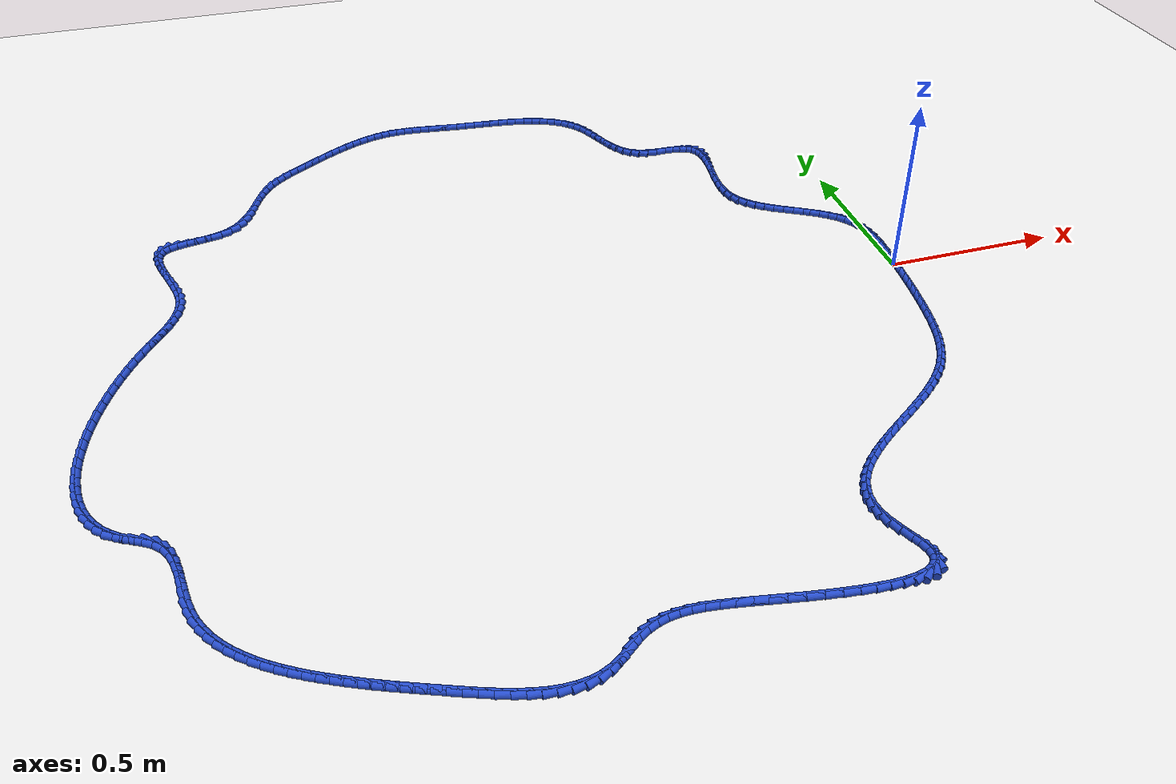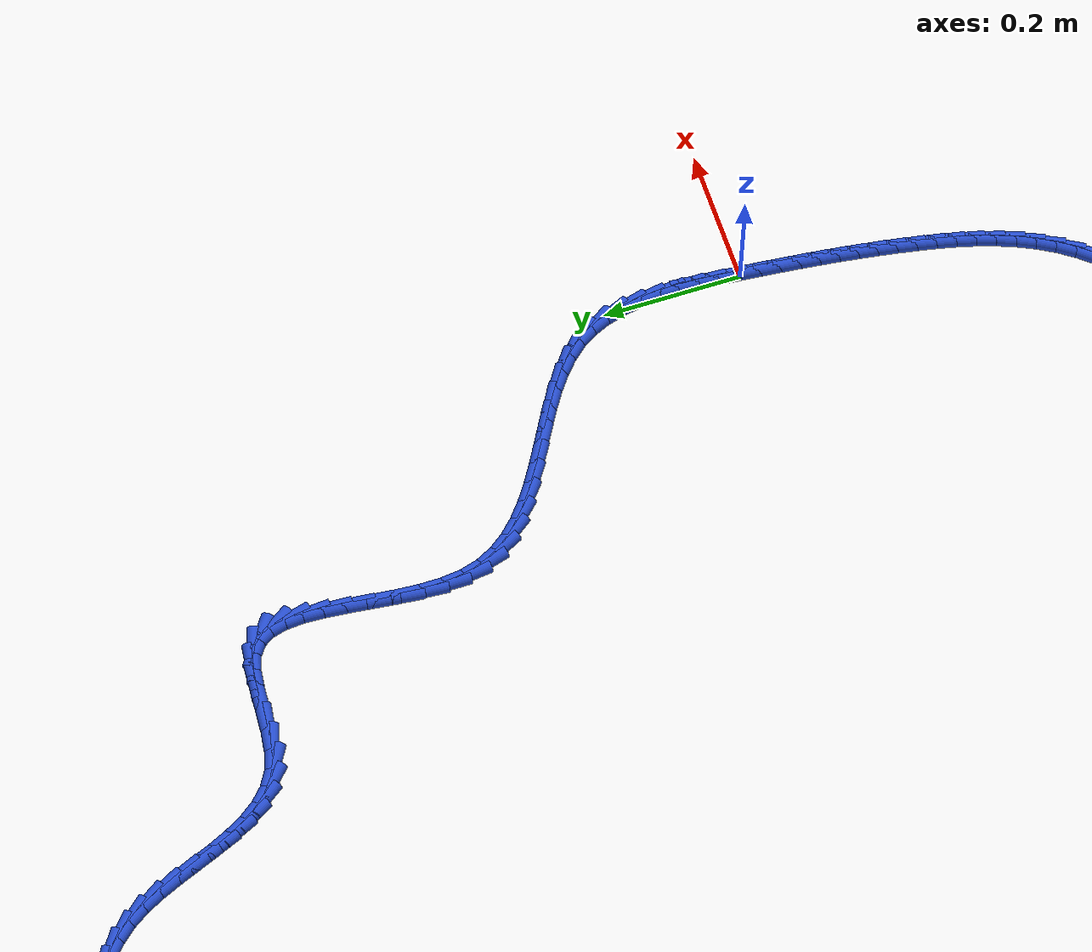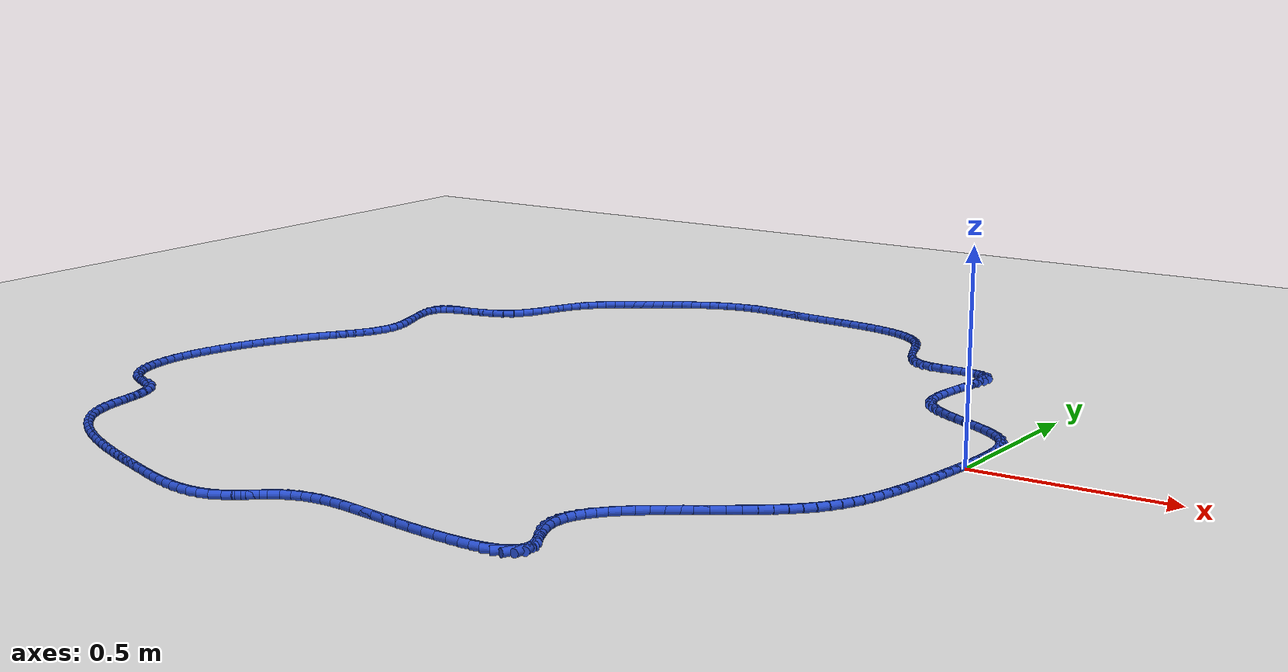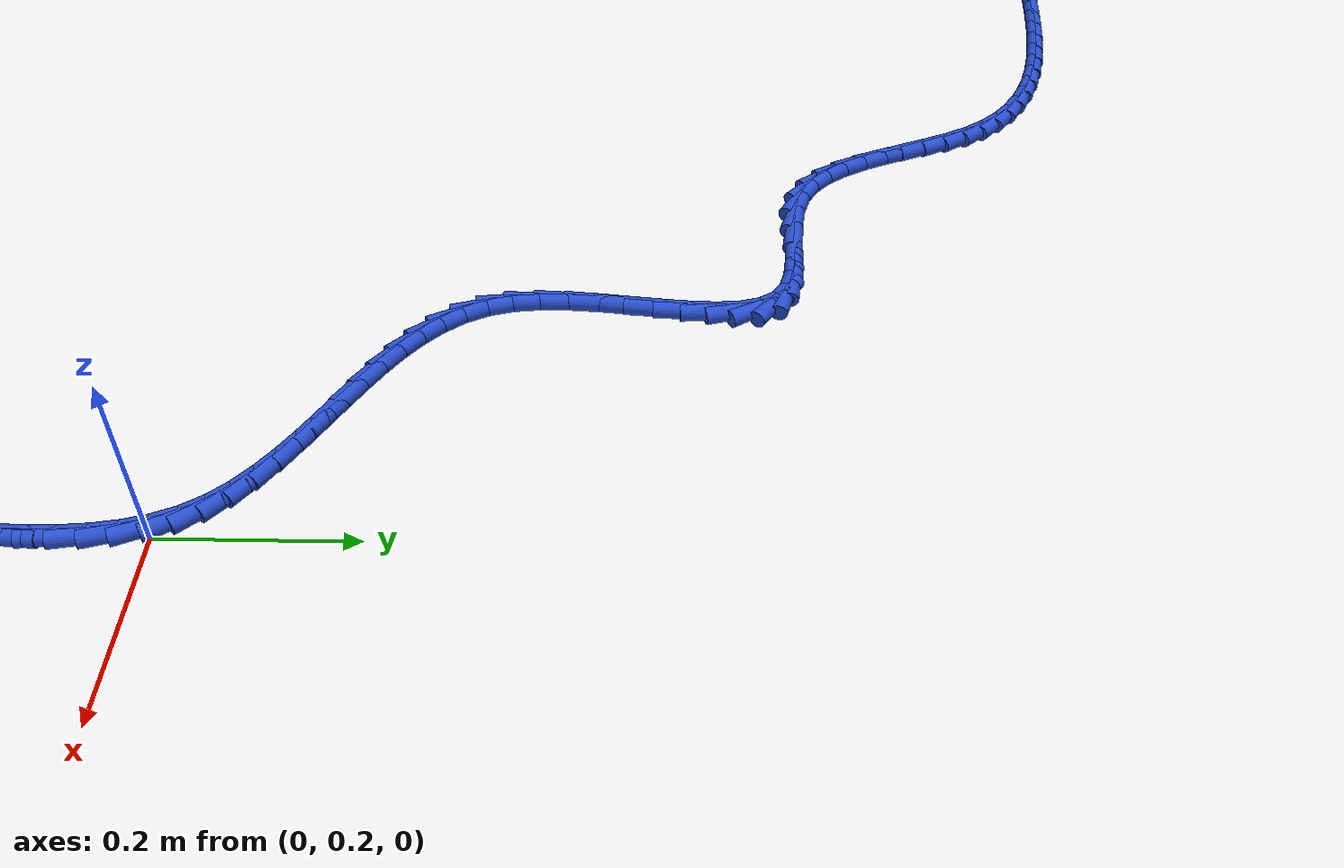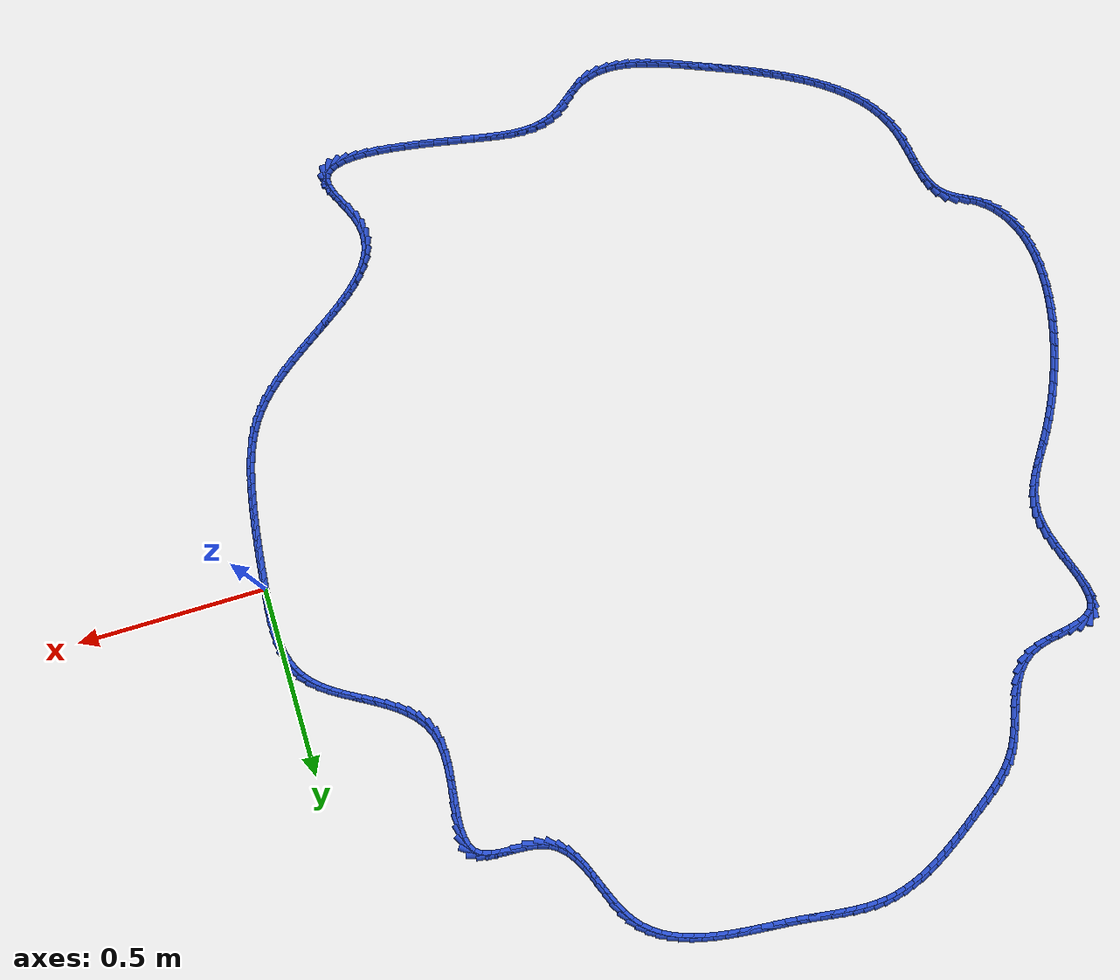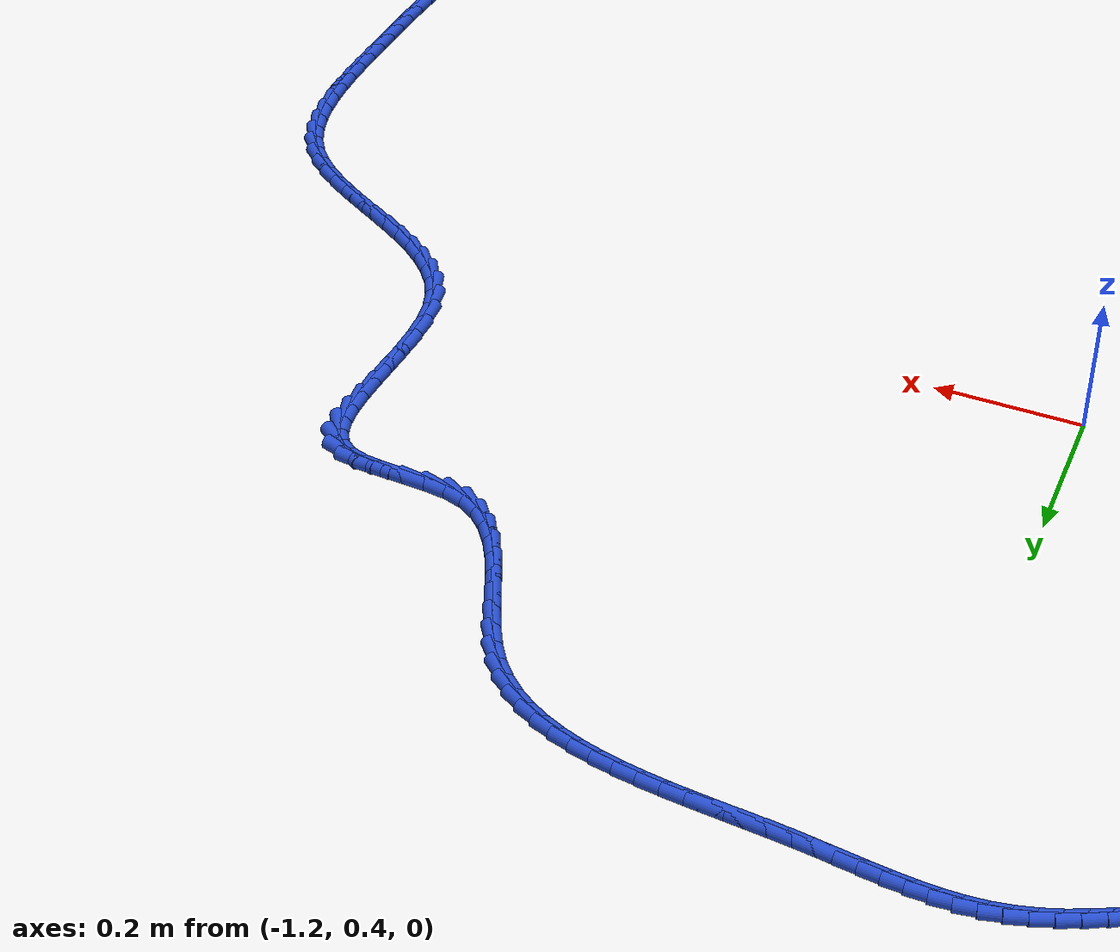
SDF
<sdf version="1.6">
 <world name="default">
  <light name="sun" type="directional">
   <pose>0 0 10 0 -0 0</pose>
   <diffuse>0.8 0.8 0.8 1</diffuse>
   <specular>0.2 0.2 0.2 1</specular>
   <attenuation>
    <range>1000</range>
    <constant>0.9</constant>
    <linear>0.01</linear>
    <quadratic>0.001</quadratic>
   </attenuation>
   <direction>-0.5 0.1 -0.9</direction>
  </light>
  <model name="ground_plane">
   <static>1</static>
   <link name="link">
    <collision name="collision">
     <geometry><plane><normal>0 0 1</normal><size>100 100</size></plane></geometry>
     <surface><friction><ode><mu>100</mu><mu2>50</mu2></ode></friction></surface>
    </collision>
    <visual name="visual">
     <cast_shadows>0</cast_shadows>
     <geometry><plane><normal>0 0 1</normal><size>100 100</size></plane></geometry>
     <material>
      <script><uri>file://media/materials/scripts/gazebo.material</uri><name>Gazebo/WhiteGlow</name></script>
     </material>
    </visual>
   </link>
  </model>
  <gravity>0 0 -9.8</gravity>
  <magnetic_field>6e-06 2.3e-05 -4.2e-05</magnetic_field>
  <atmosphere type="adiabatic"/>
  <physics name="default_physics" default="0" type="ode">
   <max_step_size>0.001</max_step_size>
   <real_time_factor>1</real_time_factor>
   <real_time_update_rate>1000</real_time_update_rate>
  </physics>
  <scene><ambient>0.4 0.4 0.4 1</ambient><background>0.7 0.7 0.7 1</background><shadows>1</shadows></scene>
  <spherical_coordinates>
   <surface_model>EARTH_WGS84</surface_model>
   <latitude_deg>0</latitude_deg>
   <longitude_deg>0</longitude_deg>
   <elevation>0</elevation>
   <heading_deg>0</heading_deg>
  </spherical_coordinates>
  <model name="line">
   <link name="link_0">
    <pose>6.938893903907228e-18 1.3877787807814457e-17 0.01 0 1.57 1.4926502074860097</pose>
    <collision name="collision">
     <geometry><cylinder><radius>0.01</radius><length>0.08</length></cylinder></geometry>
    </collision>
    <visual name="visual">
     <material>
      <script><name>Gazebo/Blue</name><uri>file://media/materials/scripts/gazebo.material</uri></script>
     </material>
     <geometry><cylinder><radius>0.01</radius><length>0.08</length></cylinder></geometry>
    </visual>
   </link>
   <link name="link_1">
    <pose>0.0023202932928651165 0.02963126240863364 0.01 0 1.57 1.5112525195098752</pose>
    <collision name="collision">
     <geometry><cylinder><radius>0.01</radius><length>0.08</length></cylinder></geometry>
    </collision>
    <visual name="visual">
     <material>
      <script><name>Gazebo/Blue</name><uri>file://media/materials/scripts/gazebo.material</uri></script>
     </material>
     <geometry><cylinder><radius>0.01</radius><length>0.08</length></cylinder></geometry>
    </visual>
   </link>
   <link name="link_2">
    <pose>0.004103257225446785 0.059539599986659454 0.01 0 1.57 1.5436425515877783</pose>
    <collision name="collision">
     <geometry><cylinder><radius>0.01</radius><length>0.08</length></cylinder></geometry>
    </collision>
    <visual name="visual">
     <material>
      <script><name>Gazebo/Blue</name><uri>file://media/materials/scripts/gazebo.material</uri></script>
     </material>
     <geometry><cylinder><radius>0.01</radius><length>0.08</length></cylinder></geometry>
    </visual>
   </link>
   <link name="link_3">
    <pose>0.004913730629263788 0.08937980427007985 0.01 0 1.57 -1.5505054672399763</pose>
    <collision name="collision">
     <geometry><cylinder><radius>0.01</radius><length>0.08</length></cylinder></geometry>
    </collision>
    <visual name="visual">
     <material>
      <script><name>Gazebo/Blue</name><uri>file://media/materials/scripts/gazebo.material</uri></script>
     </material>
     <geometry><cylinder><radius>0.01</radius><length>0.08</length></cylinder></geometry>
    </visual>
   </link>
   <link name="link_4">
    <pose>0.004316552335834899 0.11880666679489729 0.01 0 1.57 -1.4858898653459824</pose>
    <collision name="collision">
     <geometry><cylinder><radius>0.01</radius><length>0.08</length></cylinder></geometry>
    </collision>
    <visual name="visual">
     <material>
      <script><name>Gazebo/Blue</name><uri>file://media/materials/scripts/gazebo.material</uri></script>
     </material>
     <geometry><cylinder><radius>0.01</radius><length>0.08</length></cylinder></geometry>
    </visual>
   </link>
   <link name="link_5">
    <pose>0.001876561176678896 0.1474749790971142 0.01 0 1.57 -1.4012783976738419</pose>
    <collision name="collision">
     <geometry><cylinder><radius>0.01</radius><length>0.08</length></cylinder></geometry>
    </collision>
    <visual name="visual">
     <material>
      <script><name>Gazebo/Blue</name><uri>file://media/materials/scripts/gazebo.material</uri></script>
     </material>
     <geometry><cylinder><radius>0.01</radius><length>0.08</length></cylinder></geometry>
    </visual>
   </link>
   <link name="link_6">
    <pose>-0.0028414040166854504 0.17503953271273295 0.01 0 1.57 -1.2935765922307763</pose>
    <collision name="collision">
     <geometry><cylinder><radius>0.01</radius><length>0.08</length></cylinder></geometry>
    </collision>
    <visual name="visual">
     <material>
      <script><name>Gazebo/Blue</name><uri>file://media/materials/scripts/gazebo.material</uri></script>
     </material>
     <geometry><cylinder><radius>0.01</radius><length>0.08</length></cylinder></geometry>
    </visual>
   </link>
   <link name="link_7">
    <pose>-0.010272504412739364 0.20115511917775597 0.01 0 1.57 -1.160500586632022</pose>
    <collision name="collision">
     <geometry><cylinder><radius>0.01</radius><length>0.08</length></cylinder></geometry>
    </collision>
    <visual name="visual">
     <material>
      <script><name>Gazebo/Blue</name><uri>file://media/materials/scripts/gazebo.material</uri></script>
     </material>
     <geometry><cylinder><radius>0.01</radius><length>0.08</length></cylinder></geometry>
    </visual>
   </link>
   <link name="link_8">
    <pose>-0.020851901179964064 0.22547653002818574 0.01 0 1.57 -1.0030397510339848</pose>
    <collision name="collision">
     <geometry><cylinder><radius>0.01</radius><length>0.08</length></cylinder></geometry>
    </collision>
    <visual name="visual">
     <material>
      <script><name>Gazebo/Blue</name><uri>file://media/materials/scripts/gazebo.material</uri></script>
     </material>
     <geometry><cylinder><radius>0.01</radius><length>0.08</length></cylinder></geometry>
    </visual>
   </link>
   <link name="link_9">
    <pose>-0.03500438931396423 0.24766579175591782 0.01 0 1.57 -0.8463104783337656</pose>
    <collision name="collision">
     <geometry><cylinder><radius>0.01</radius><length>0.08</length></cylinder></geometry>
    </collision>
    <visual name="visual">
     <material>
      <script><name>Gazebo/Blue</name><uri>file://media/materials/scripts/gazebo.material</uri></script>
     </material>
     <geometry><cylinder><radius>0.01</radius><length>0.08</length></cylinder></geometry>
    </visual>
   </link>
   <link name="link_10">
    <pose>-0.05272314583087124 0.2676861738555821 0.01 0 1.57 -0.721702423346588</pose>
    <collision name="collision">
     <geometry><cylinder><radius>0.01</radius><length>0.08</length></cylinder></geometry>
    </collision>
    <visual name="visual">
     <material>
      <script><name>Gazebo/Blue</name><uri>file://media/materials/scripts/gazebo.material</uri></script>
     </material>
     <geometry><cylinder><radius>0.01</radius><length>0.08</length></cylinder></geometry>
    </visual>
   </link>
   <link name="link_11">
    <pose>-0.07342350970037664 0.2859042415056813 0.01 0 1.57 -0.6299822140444941</pose>
    <collision name="collision">
     <geometry><cylinder><radius>0.01</radius><length>0.08</length></cylinder></geometry>
    </collision>
    <visual name="visual">
     <material>
      <script><name>Gazebo/Blue</name><uri>file://media/materials/scripts/gazebo.material</uri></script>
     </material>
     <geometry><cylinder><radius>0.01</radius><length>0.08</length></cylinder></geometry>
    </visual>
   </link>
   <link name="link_12">
    <pose>-0.09648042715843243 0.30271475154720484 0.01 0 1.57 -0.5673968668931678</pose>
    <collision name="collision">
     <geometry><cylinder><radius>0.01</radius><length>0.08</length></cylinder></geometry>
    </collision>
    <visual name="visual">
     <material>
      <script><name>Gazebo/Blue</name><uri>file://media/materials/scripts/gazebo.material</uri></script>
     </material>
     <geometry><cylinder><radius>0.01</radius><length>0.08</length></cylinder></geometry>
    </visual>
   </link>
   <link name="link_13">
    <pose>-0.12126884444099065 0.31851246082114204 0.01 0 1.57 -0.5302134122754102</pose>
    <collision name="collision">
     <geometry><cylinder><radius>0.01</radius><length>0.08</length></cylinder></geometry>
    </collision>
    <visual name="visual">
     <material>
      <script><name>Gazebo/Blue</name><uri>file://media/materials/scripts/gazebo.material</uri></script>
     </material>
     <geometry><cylinder><radius>0.01</radius><length>0.08</length></cylinder></geometry>
    </visual>
   </link>
   <link name="link_14">
    <pose>-0.14716370778400326 0.33369212616848204 0.01 0 1.57 -0.5158311585512316</pose>
    <collision name="collision">
     <geometry><cylinder><radius>0.01</radius><length>0.08</length></cylinder></geometry>
    </collision>
    <visual name="visual">
     <material>
      <script><name>Gazebo/Blue</name><uri>file://media/materials/scripts/gazebo.material</uri></script>
     </material>
     <geometry><cylinder><radius>0.01</radius><length>0.08</length></cylinder></geometry>
    </visual>
   </link>
   <link name="link_15">
    <pose>-0.17353996342342232 0.34864850443021417 0.01 0 1.57 -0.5230969465022173</pose>
    <collision name="collision">
     <geometry><cylinder><radius>0.01</radius><length>0.08</length></cylinder></geometry>
    </collision>
    <visual name="visual">
     <material>
      <script><name>Gazebo/Blue</name><uri>file://media/materials/scripts/gazebo.material</uri></script>
     </material>
     <geometry><cylinder><radius>0.01</radius><length>0.08</length></cylinder></geometry>
    </visual>
   </link>
   <link name="link_16">
    <pose>-0.1997725575951998 0.3637763524473276 0.01 0 1.57 -0.5523381844660998</pose>
    <collision name="collision">
     <geometry><cylinder><radius>0.01</radius><length>0.08</length></cylinder></geometry>
    </collision>
    <visual name="visual">
     <material>
      <script><name>Gazebo/Blue</name><uri>file://media/materials/scripts/gazebo.material</uri></script>
     </material>
     <geometry><cylinder><radius>0.01</radius><length>0.08</length></cylinder></geometry>
    </visual>
   </link>
   <link name="link_17">
    <pose>-0.22523643653528777 0.3794704270608117 0.01 0 1.57 -0.6052956724535428</pose>
    <collision name="collision">
     <geometry><cylinder><radius>0.01</radius><length>0.08</length></cylinder></geometry>
    </collision>
    <visual name="visual">
     <material>
      <script><name>Gazebo/Blue</name><uri>file://media/materials/scripts/gazebo.material</uri></script>
     </material>
     <geometry><cylinder><radius>0.01</radius><length>0.08</length></cylinder></geometry>
    </visual>
   </link>
   <link name="link_18">
    <pose>-0.24930654647963815 0.39612548511165563 0.01 0 1.57 -0.6848823754854073</pose>
    <collision name="collision">
     <geometry><cylinder><radius>0.01</radius><length>0.08</length></cylinder></geometry>
    </collision>
    <visual name="visual">
     <material>
      <script><name>Gazebo/Blue</name><uri>file://media/materials/scripts/gazebo.material</uri></script>
     </material>
     <geometry><cylinder><radius>0.01</radius><length>0.08</length></cylinder></geometry>
    </visual>
   </link>
   <link name="link_19">
    <pose>-0.2713578336642029 0.41413628344084863 0.01 0 1.57 -0.7944328034026182</pose>
    <collision name="collision">
     <geometry><cylinder><radius>0.01</radius><length>0.08</length></cylinder></geometry>
    </collision>
    <visual name="visual">
     <material>
      <script><name>Gazebo/Blue</name><uri>file://media/materials/scripts/gazebo.material</uri></script>
     </material>
     <geometry><cylinder><radius>0.01</radius><length>0.08</length></cylinder></geometry>
    </visual>
   </link>
   <link name="link_20">
    <pose>-0.29076524432493434 0.4338975788893802 0.01 0 1.57 -0.9358639048798788</pose>
    <collision name="collision">
     <geometry><cylinder><radius>0.01</radius><length>0.08</length></cylinder></geometry>
    </collision>
    <visual name="visual">
     <material>
      <script><name>Gazebo/Blue</name><uri>file://media/materials/scripts/gazebo.material</uri></script>
     </material>
     <geometry><cylinder><radius>0.01</radius><length>0.08</length></cylinder></geometry>
    </visual>
   </link>
   <link name="link_21">
    <pose>-0.30690372469778404 0.45580412829823924 0.01 0 1.57 -1.1064546700520779</pose>
    <collision name="collision">
     <geometry><cylinder><radius>0.01</radius><length>0.08</length></cylinder></geometry>
    </collision>
    <visual name="visual">
     <material>
      <script><name>Gazebo/Blue</name><uri>file://media/materials/scripts/gazebo.material</uri></script>
     </material>
     <geometry><cylinder><radius>0.01</radius><length>0.08</length></cylinder></geometry>
    </visual>
   </link>
   <link name="link_22">
    <pose>-0.3191482210187043 0.48025068850841524 0.01 0 1.57 -1.294887156933358</pose>
    <collision name="collision">
     <geometry><cylinder><radius>0.01</radius><length>0.08</length></cylinder></geometry>
    </collision>
    <visual name="visual">
     <material>
      <script><name>Gazebo/Blue</name><uri>file://media/materials/scripts/gazebo.material</uri></script>
     </material>
     <geometry><cylinder><radius>0.01</radius><length>0.08</length></cylinder></geometry>
    </visual>
   </link>
   <link name="link_23">
    <pose>-0.32689605594745785 0.5076155865667633 0.01 0 1.57 -1.4591172901791665</pose>
    <collision name="collision">
     <geometry><cylinder><radius>0.01</radius><length>0.08</length></cylinder></geometry>
    </collision>
    <visual name="visual">
     <material>
      <script><name>Gazebo/Blue</name><uri>file://media/materials/scripts/gazebo.material</uri></script>
     </material>
     <geometry><cylinder><radius>0.01</radius><length>0.08</length></cylinder></geometry>
    </visual>
   </link>
   <link name="link_24">
    <pose>-0.3302745105603986 0.537741180653424 0.01 0 1.57 -1.570460866137799</pose>
    <collision name="collision">
     <geometry><cylinder><radius>0.01</radius><length>0.08</length></cylinder></geometry>
    </collision>
    <visual name="visual">
     <material>
      <script><name>Gazebo/Blue</name><uri>file://media/materials/scripts/gazebo.material</uri></script>
     </material>
     <geometry><cylinder><radius>0.01</radius><length>0.08</length></cylinder></geometry>
    </visual>
   </link>
   <link name="link_25">
    <pose>-0.33028527435863436 0.569827798276914 0.01 0 1.57 1.5015405704622893</pose>
    <collision name="collision">
     <geometry><cylinder><radius>0.01</radius><length>0.08</length></cylinder></geometry>
    </collision>
    <visual name="visual">
     <material>
      <script><name>Gazebo/Blue</name><uri>file://media/materials/scripts/gazebo.material</uri></script>
     </material>
     <geometry><cylinder><radius>0.01</radius><length>0.08</length></cylinder></geometry>
    </visual>
   </link>
   <link name="link_26">
    <pose>-0.32798159884435163 0.6030379077654799 0.01 0 1.57 1.4647691158746887</pose>
    <collision name="collision">
     <geometry><cylinder><radius>0.01</radius><length>0.08</length></cylinder></geometry>
    </collision>
    <visual name="visual">
     <material>
      <script><name>Gazebo/Blue</name><uri>file://media/materials/scripts/gazebo.material</uri></script>
     </material>
     <geometry><cylinder><radius>0.01</radius><length>0.08</length></cylinder></geometry>
    </visual>
   </link>
   <link name="link_27">
    <pose>-0.3244167355197362 0.6365339774473685 0.01 0 1.57 1.456773189536596</pose>
    <collision name="collision">
     <geometry><cylinder><radius>0.01</radius><length>0.08</length></cylinder></geometry>
    </collision>
    <visual name="visual">
     <material>
      <script><name>Gazebo/Blue</name><uri>file://media/materials/scripts/gazebo.material</uri></script>
     </material>
     <geometry><cylinder><radius>0.01</radius><length>0.08</length></cylinder></geometry>
    </visual>
   </link>
   <link name="link_28">
    <pose>-0.3206439358869746 0.6694784756508259 0.01 0 1.57 1.4782882539731652</pose>
    <collision name="collision">
     <geometry><cylinder><radius>0.01</radius><length>0.08</length></cylinder></geometry>
    </collision>
    <visual name="visual">
     <material>
      <script><name>Gazebo/Blue</name><uri>file://media/materials/scripts/gazebo.material</uri></script>
     </material>
     <geometry><cylinder><radius>0.01</radius><length>0.08</length></cylinder></geometry>
    </visual>
   </link>
   <link name="link_29">
    <pose>-0.317716451448253 0.7010338707040993 0.01 0 1.57 1.535728498206944</pose>
    <collision name="collision">
     <geometry><cylinder><radius>0.01</radius><length>0.08</length></cylinder></geometry>
    </collision>
    <visual name="visual">
     <material>
      <script><name>Gazebo/Blue</name><uri>file://media/materials/scripts/gazebo.material</uri></script>
     </material>
     <geometry><cylinder><radius>0.01</radius><length>0.08</length></cylinder></geometry>
    </visual>
   </link>
   <link name="link_30">
    <pose>-0.31668753370575736 0.7303626309354347 0.01 0 1.57 -1.4977140685590402</pose>
    <collision name="collision">
     <geometry><cylinder><radius>0.01</radius><length>0.08</length></cylinder></geometry>
    </collision>
    <visual name="visual">
     <material>
      <script><name>Gazebo/Blue</name><uri>file://media/materials/scripts/gazebo.material</uri></script>
     </material>
     <geometry><cylinder><radius>0.01</radius><length>0.08</length></cylinder></geometry>
    </visual>
   </link>
   <link name="link_31">
    <pose>-0.31861043416167395 0.7566272246730791 0.01 0 1.57 -1.311675270644913</pose>
    <collision name="collision">
     <geometry><cylinder><radius>0.01</radius><length>0.08</length></cylinder></geometry>
    </collision>
    <visual name="visual">
     <material>
      <script><name>Gazebo/Blue</name><uri>file://media/materials/scripts/gazebo.material</uri></script>
     </material>
     <geometry><cylinder><radius>0.01</radius><length>0.08</length></cylinder></geometry>
    </visual>
   </link>
   <link name="link_32">
    <pose>-0.3245384043181891 0.7789901202452789 0.01 0 1.57 -1.0133607353532903</pose>
    <collision name="collision">
     <geometry><cylinder><radius>0.01</radius><length>0.08</length></cylinder></geometry>
    </collision>
    <visual name="visual">
     <material>
      <script><name>Gazebo/Blue</name><uri>file://media/materials/scripts/gazebo.material</uri></script>
     </material>
     <geometry><cylinder><radius>0.01</radius><length>0.08</length></cylinder></geometry>
    </visual>
   </link>
   <link name="link_33">
    <pose>-0.33552469567748877 0.796613785980281 0.01 0 1.57 -0.6149619780375356</pose>
    <collision name="collision">
     <geometry><cylinder><radius>0.01</radius><length>0.08</length></cylinder></geometry>
    </collision>
    <visual name="visual">
     <material>
      <script><name>Gazebo/Blue</name><uri>file://media/materials/scripts/gazebo.material</uri></script>
     </material>
     <geometry><cylinder><radius>0.01</radius><length>0.08</length></cylinder></geometry>
    </visual>
   </link>
   <link name="link_34">
    <pose>-0.35260465458649803 0.8086778813732771 0.01 0 1.57 -0.2820225873372577</pose>
    <collision name="collision">
     <geometry><cylinder><radius>0.01</radius><length>0.08</length></cylinder></geometry>
    </collision>
    <visual name="visual">
     <material>
      <script><name>Gazebo/Blue</name><uri>file://media/materials/scripts/gazebo.material</uri></script>
     </material>
     <geometry><cylinder><radius>0.01</radius><length>0.08</length></cylinder></geometry>
    </visual>
   </link>
   <link name="link_35">
    <pose>-0.37574931229785646 0.8153839402456678 0.01 0 1.57 -0.11310902173831741</pose>
    <collision name="collision">
     <geometry><cylinder><radius>0.01</radius><length>0.08</length></cylinder></geometry>
    </collision>
    <visual name="visual">
     <material>
      <script><name>Gazebo/Blue</name><uri>file://media/materials/scripts/gazebo.material</uri></script>
     </material>
     <geometry><cylinder><radius>0.01</radius><length>0.08</length></cylinder></geometry>
    </visual>
   </link>
   <link name="link_36">
    <pose>-0.40328573282687336 0.8185119086033424 0.01 0 1.57 -0.04860806008312421</pose>
    <collision name="collision">
     <geometry><cylinder><radius>0.01</radius><length>0.08</length></cylinder></geometry>
    </collision>
    <visual name="visual">
     <material>
      <script><name>Gazebo/Blue</name><uri>file://media/materials/scripts/gazebo.material</uri></script>
     </material>
     <geometry><cylinder><radius>0.01</radius><length>0.08</length></cylinder></geometry>
    </visual>
   </link>
   <link name="link_37">
    <pose>-0.4334002302172056 0.8199768698595419 0.01 0 1.57 -0.055548345752630394</pose>
    <collision name="collision">
     <geometry><cylinder><radius>0.01</radius><length>0.08</length></cylinder></geometry>
    </collision>
    <visual name="visual">
     <material>
      <script><name>Gazebo/Blue</name><uri>file://media/materials/scripts/gazebo.material</uri></script>
     </material>
     <geometry><cylinder><radius>0.01</radius><length>0.08</length></cylinder></geometry>
    </visual>
   </link>
   <link name="link_38">
    <pose>-0.46427911851251036 0.8216939074275069 0.01 0 1.57 -0.12948434203049283</pose>
    <collision name="collision">
     <geometry><cylinder><radius>0.01</radius><length>0.08</length></cylinder></geometry>
    </collision>
    <visual name="visual">
     <material>
      <script><name>Gazebo/Blue</name><uri>file://media/materials/scripts/gazebo.material</uri></script>
     </material>
     <geometry><cylinder><radius>0.01</radius><length>0.08</length></cylinder></geometry>
    </visual>
   </link>
   <link name="link_39">
    <pose>-0.49410871175644394 0.8255781047204782 0.01 0 1.57 -0.2872287206106882</pose>
    <collision name="collision">
     <geometry><cylinder><radius>0.01</radius><length>0.08</length></cylinder></geometry>
    </collision>
    <visual name="visual">
     <material>
      <script><name>Gazebo/Blue</name><uri>file://media/materials/scripts/gazebo.material</uri></script>
     </material>
     <geometry><cylinder><radius>0.01</radius><length>0.08</length></cylinder></geometry>
    </visual>
   </link>
   <link name="link_40">
    <pose>-0.521075732464282 0.8335440874086932 0.01 0 1.57 -0.5282831732961094</pose>
    <collision name="collision">
     <geometry><cylinder><radius>0.01</radius><length>0.08</length></cylinder></geometry>
    </collision>
    <visual name="visual">
     <material>
      <script><name>Gazebo/Blue</name><uri>file://media/materials/scripts/gazebo.material</uri></script>
     </material>
     <geometry><cylinder><radius>0.01</radius><length>0.08</length></cylinder></geometry>
    </visual>
   </link>
   <link name="link_41">
    <pose>-0.5439260825493923 0.8468798514397184 0.01 0 1.57 -0.758006615489746</pose>
    <collision name="collision">
     <geometry><cylinder><radius>0.01</radius><length>0.08</length></cylinder></geometry>
    </collision>
    <visual name="visual">
     <material>
      <script><name>Gazebo/Blue</name><uri>file://media/materials/scripts/gazebo.material</uri></script>
     </material>
     <geometry><cylinder><radius>0.01</radius><length>0.08</length></cylinder></geometry>
    </visual>
   </link>
   <link name="link_42">
    <pose>-0.56307269899656 0.8650052736421964 0.01 0 1.57 -0.9368571467097474</pose>
    <collision name="collision">
     <geometry><cylinder><radius>0.01</radius><length>0.08</length></cylinder></geometry>
    </collision>
    <visual name="visual">
     <material>
      <script><name>Gazebo/Blue</name><uri>file://media/materials/scripts/gazebo.material</uri></script>
     </material>
     <geometry><cylinder><radius>0.01</radius><length>0.08</length></cylinder></geometry>
    </visual>
   </link>
   <link name="link_43">
    <pose>-0.5792377932902318 0.8869936504903903 0.01 0 1.57 -1.0618978864356188</pose>
    <collision name="collision">
     <geometry><cylinder><radius>0.01</radius><length>0.08</length></cylinder></geometry>
    </collision>
    <visual name="visual">
     <material>
      <script><name>Gazebo/Blue</name><uri>file://media/materials/scripts/gazebo.material</uri></script>
     </material>
     <geometry><cylinder><radius>0.01</radius><length>0.08</length></cylinder></geometry>
    </visual>
   </link>
   <link name="link_44">
    <pose>-0.5931435769148546 0.9119182784585632 0.01 0 1.57 -1.1403024016664975</pose>
    <collision name="collision">
     <geometry><cylinder><radius>0.01</radius><length>0.08</length></cylinder></geometry>
    </collision>
    <visual name="visual">
     <material>
      <script><name>Gazebo/Blue</name><uri>file://media/materials/scripts/gazebo.material</uri></script>
     </material>
     <geometry><cylinder><radius>0.01</radius><length>0.08</length></cylinder></geometry>
    </visual>
   </link>
   <link name="link_45">
    <pose>-0.6055122613548761 0.9388524540209787 0.01 0 1.57 -1.1796590871038244</pose>
    <collision name="collision">
     <geometry><cylinder><radius>0.01</radius><length>0.08</length></cylinder></geometry>
    </collision>
    <visual name="visual">
     <material>
      <script><name>Gazebo/Blue</name><uri>file://media/materials/scripts/gazebo.material</uri></script>
     </material>
     <geometry><cylinder><radius>0.01</radius><length>0.08</length></cylinder></geometry>
    </visual>
   </link>
   <link name="link_46">
    <pose>-0.6170660580947434 0.9668694736519001 0.01 0 1.57 -1.184433164939543</pose>
    <collision name="collision">
     <geometry><cylinder><radius>0.01</radius><length>0.08</length></cylinder></geometry>
    </collision>
    <visual name="visual">
     <material>
      <script><name>Gazebo/Blue</name><uri>file://media/materials/scripts/gazebo.material</uri></script>
     </material>
     <geometry><cylinder><radius>0.01</radius><length>0.08</length></cylinder></geometry>
    </visual>
   </link>
   <link name="link_47">
    <pose>-0.628527178618903 0.9950426338255903 0.01 0 1.57 -1.1552652935465182</pose>
    <collision name="collision">
     <geometry><cylinder><radius>0.01</radius><length>0.08</length></cylinder></geometry>
    </collision>
    <visual name="visual">
     <material>
      <script><name>Gazebo/Blue</name><uri>file://media/materials/scripts/gazebo.material</uri></script>
     </material>
     <geometry><cylinder><radius>0.01</radius><length>0.08</length></cylinder></geometry>
    </visual>
   </link>
   <link name="link_48">
    <pose>-0.6406178344118023 1.0224452310163121 0.01 0 1.57 -1.0889638499875638</pose>
    <collision name="collision">
     <geometry><cylinder><radius>0.01</radius><length>0.08</length></cylinder></geometry>
    </collision>
    <visual name="visual">
     <material>
      <script><name>Gazebo/Blue</name><uri>file://media/materials/scripts/gazebo.material</uri></script>
     </material>
     <geometry><cylinder><radius>0.01</radius><length>0.08</length></cylinder></geometry>
    </visual>
   </link>
   <link name="link_49">
    <pose>-0.6540602369578885 1.0481505616983293 0.01 0 1.57 -0.9799105884819208</pose>
    <collision name="collision">
     <geometry><cylinder><radius>0.01</radius><length>0.08</length></cylinder></geometry>
    </collision>
    <visual name="visual">
     <material>
      <script><name>Gazebo/Blue</name><uri>file://media/materials/scripts/gazebo.material</uri></script>
     </material>
     <geometry><cylinder><radius>0.01</radius><length>0.08</length></cylinder></geometry>
    </visual>
   </link>
   <link name="link_50">
    <pose>-0.6695590361818266 1.071254158830559 0.01 0 1.57 -0.8462894560027613</pose>
    <collision name="collision">
     <geometry><cylinder><radius>0.01</radius><length>0.08</length></cylinder></geometry>
    </collision>
    <visual name="visual">
     <material>
      <script><name>Gazebo/Blue</name><uri>file://media/materials/scripts/gazebo.material</uri></script>
     </material>
     <geometry><cylinder><radius>0.01</radius><length>0.08</length></cylinder></geometry>
    </visual>
   </link>
   <link name="link_51">
    <pose>-0.6873875527972113 1.091397705343889 0.01 0 1.57 -0.716130384689412</pose>
    <collision name="collision">
     <geometry><cylinder><radius>0.01</radius><length>0.08</length></cylinder></geometry>
    </collision>
    <visual name="visual">
     <material>
      <script><name>Gazebo/Blue</name><uri>file://media/materials/scripts/gazebo.material</uri></script>
     </material>
     <geometry><cylinder><radius>0.01</radius><length>0.08</length></cylinder></geometry>
    </visual>
   </link>
   <link name="link_52">
    <pose>-0.7073719755624859 1.1087890436096202 0.01 0 1.57 -0.5956193176208316</pose>
    <collision name="collision">
     <geometry><cylinder><radius>0.01</radius><length>0.08</length></cylinder></geometry>
    </collision>
    <visual name="visual">
     <material>
      <script><name>Gazebo/Blue</name><uri>file://media/materials/scripts/gazebo.material</uri></script>
     </material>
     <geometry><cylinder><radius>0.01</radius><length>0.08</length></cylinder></geometry>
    </visual>
   </link>
   <link name="link_53">
    <pose>-0.7293177698446713 1.1236622560017093 0.01 0 1.57 -0.4880653245454407</pose>
    <collision name="collision">
     <geometry><cylinder><radius>0.01</radius><length>0.08</length></cylinder></geometry>
    </collision>
    <visual name="visual">
     <material>
      <script><name>Gazebo/Blue</name><uri>file://media/materials/scripts/gazebo.material</uri></script>
     </material>
     <geometry><cylinder><radius>0.01</radius><length>0.08</length></cylinder></geometry>
    </visual>
   </link>
   <link name="link_54">
    <pose>-0.7530304010107903 1.1362514248941138 0.01 0 1.57 -0.3949198030846811</pose>
    <collision name="collision">
     <geometry><cylinder><radius>0.01</radius><length>0.08</length></cylinder></geometry>
    </collision>
    <visual name="visual">
     <material>
      <script><name>Gazebo/Blue</name><uri>file://media/materials/scripts/gazebo.material</uri></script>
     </material>
     <geometry><cylinder><radius>0.01</radius><length>0.08</length></cylinder></geometry>
    </visual>
   </link>
   <link name="link_55">
    <pose>-0.7783153344278642 1.1467906326607893 0.01 0 1.57 -0.31619649093261326</pose>
    <collision name="collision">
     <geometry><cylinder><radius>0.01</radius><length>0.08</length></cylinder></geometry>
    </collision>
    <visual name="visual">
     <material>
      <script><name>Gazebo/Blue</name><uri>file://media/materials/scripts/gazebo.material</uri></script>
     </material>
     <geometry><cylinder><radius>0.01</radius><length>0.08</length></cylinder></geometry>
    </visual>
   </link>
   <link name="link_56">
    <pose>-0.8049780354629145 1.1555139616756922 0.01 0 1.57 -0.2510549004785778</pose>
    <collision name="collision">
     <geometry><cylinder><radius>0.01</radius><length>0.08</length></cylinder></geometry>
    </collision>
    <visual name="visual">
     <material>
      <script><name>Gazebo/Blue</name><uri>file://media/materials/scripts/gazebo.material</uri></script>
     </material>
     <geometry><cylinder><radius>0.01</radius><length>0.08</length></cylinder></geometry>
    </visual>
   </link>
   <link name="link_57">
    <pose>-0.8328239694829632 1.1626554943127796 0.01 0 1.57 -0.19829216227261964</pose>
    <collision name="collision">
     <geometry><cylinder><radius>0.01</radius><length>0.08</length></cylinder></geometry>
    </collision>
    <visual name="visual">
     <material>
      <script><name>Gazebo/Blue</name><uri>file://media/materials/scripts/gazebo.material</uri></script>
     </material>
     <geometry><cylinder><radius>0.01</radius><length>0.08</length></cylinder></geometry>
    </visual>
   </link>
   <link name="link_58">
    <pose>-0.8616586018550323 1.1684493129460078 0.01 0 1.57 -0.156666288737514</pose>
    <collision name="collision">
     <geometry><cylinder><radius>0.01</radius><length>0.08</length></cylinder></geometry>
    </collision>
    <visual name="visual">
     <material>
      <script><name>Gazebo/Blue</name><uri>file://media/materials/scripts/gazebo.material</uri></script>
     </material>
     <geometry><cylinder><radius>0.01</radius><length>0.08</length></cylinder></geometry>
    </visual>
   </link>
   <link name="link_59">
    <pose>-0.8912873979461434 1.1731294999493336 0.01 0 1.57 -0.1250742803904847</pose>
    <collision name="collision">
     <geometry><cylinder><radius>0.01</radius><length>0.08</length></cylinder></geometry>
    </collision>
    <visual name="visual">
     <material>
      <script><name>Gazebo/Blue</name><uri>file://media/materials/scripts/gazebo.material</uri></script>
     </material>
     <geometry><cylinder><radius>0.01</radius><length>0.08</length></cylinder></geometry>
    </visual>
   </link>
   <link name="link_60">
    <pose>-0.9215158231233183 1.1769301376967132 0.01 0 1.57 -0.10263542117661491</pose>
    <collision name="collision">
     <geometry><cylinder><radius>0.01</radius><length>0.08</length></cylinder></geometry>
    </collision>
    <visual name="visual">
     <material>
      <script><name>Gazebo/Blue</name><uri>file://media/materials/scripts/gazebo.material</uri></script>
     </material>
     <geometry><cylinder><radius>0.01</radius><length>0.08</length></cylinder></geometry>
    </visual>
   </link>
   <link name="link_61">
    <pose>-0.9521493427535788 1.1800853085621037 0.01 0 1.57 -0.08872312350799336</pose>
    <collision name="collision">
     <geometry><cylinder><radius>0.01</radius><length>0.08</length></cylinder></geometry>
    </collision>
    <visual name="visual">
     <material>
      <script><name>Gazebo/Blue</name><uri>file://media/materials/scripts/gazebo.material</uri></script>
     </material>
     <geometry><cylinder><radius>0.01</radius><length>0.08</length></cylinder></geometry>
    </visual>
   </link>
   <link name="link_62">
    <pose>-0.9829934222039466 1.1828290949194606 0.01 0 1.57 -0.08297417368061272</pose>
    <collision name="collision">
     <geometry><cylinder><radius>0.01</radius><length>0.08</length></cylinder></geometry>
    </collision>
    <visual name="visual">
     <material>
      <script><name>Gazebo/Blue</name><uri>file://media/materials/scripts/gazebo.material</uri></script>
     </material>
     <geometry><cylinder><radius>0.01</radius><length>0.08</length></cylinder></geometry>
    </visual>
   </link>
   <link name="link_63">
    <pose>-1.0138535268414437 1.1853955791427417 0.01 0 1.57 -0.08529218107785712</pose>
    <collision name="collision">
     <geometry><cylinder><radius>0.01</radius><length>0.08</length></cylinder></geometry>
    </collision>
    <visual name="visual">
     <material>
      <script><name>Gazebo/Blue</name><uri>file://media/materials/scripts/gazebo.material</uri></script>
     </material>
     <geometry><cylinder><radius>0.01</radius><length>0.08</length></cylinder></geometry>
    </visual>
   </link>
   <link name="link_64">
    <pose>-1.0445351220330914 1.1880188436059025 0.01 0 1.57 -0.09585402484050758</pose>
    <collision name="collision">
     <geometry><cylinder><radius>0.01</radius><length>0.08</length></cylinder></geometry>
    </collision>
    <visual name="visual">
     <material>
      <script><name>Gazebo/Blue</name><uri>file://media/materials/scripts/gazebo.material</uri></script>
     </material>
     <geometry><cylinder><radius>0.01</radius><length>0.08</length></cylinder></geometry>
    </visual>
   </link>
   <link name="link_65">
    <pose>-1.074843673145912 1.1909329706829004 0.01 0 1.57 -0.11321383145490625</pose>
    <collision name="collision">
     <geometry><cylinder><radius>0.01</radius><length>0.08</length></cylinder></geometry>
    </collision>
    <visual name="visual">
     <material>
      <script><name>Gazebo/Blue</name><uri>file://media/materials/scripts/gazebo.material</uri></script>
     </material>
     <geometry><cylinder><radius>0.01</radius><length>0.08</length></cylinder></geometry>
    </visual>
   </link>
   <link name="link_66">
    <pose>-1.1046064268935682 1.1943169965444433 0.01 0 1.57 -0.1245438298746847</pose>
    <collision name="collision">
     <geometry><cylinder><radius>0.01</radius><length>0.08</length></cylinder></geometry>
    </collision>
    <visual name="visual">
     <material>
      <script><name>Gazebo/Blue</name><uri>file://media/materials/scripts/gazebo.material</uri></script>
     </material>
     <geometry><cylinder><radius>0.01</radius><length>0.08</length></cylinder></geometry>
    </visual>
   </link>
   <link name="link_67">
    <pose>-1.133800254337698 1.1979718240710742 0.01 0 1.57 -0.1238253846497848</pose>
    <collision name="collision">
     <geometry><cylinder><radius>0.01</radius><length>0.08</length></cylinder></geometry>
    </collision>
    <visual name="visual">
     <material>
      <script><name>Gazebo/Blue</name><uri>file://media/materials/scripts/gazebo.material</uri></script>
     </material>
     <geometry><cylinder><radius>0.01</radius><length>0.08</length></cylinder></geometry>
    </visual>
   </link>
   <link name="link_68">
    <pose>-1.162464890086633 1.2015394862798119 0.01 0 1.57 -0.11035508006265995</pose>
    <collision name="collision">
     <geometry><cylinder><radius>0.01</radius><length>0.08</length></cylinder></geometry>
    </collision>
    <visual name="visual">
     <material>
      <script><name>Gazebo/Blue</name><uri>file://media/materials/scripts/gazebo.material</uri></script>
     </material>
     <geometry><cylinder><radius>0.01</radius><length>0.08</length></cylinder></geometry>
    </visual>
   </link>
   <link name="link_69">
    <pose>-1.190640285649399 1.204661468032417 0.01 0 1.57 -0.08340188536008424</pose>
    <collision name="collision">
     <geometry><cylinder><radius>0.01</radius><length>0.08</length></cylinder></geometry>
    </collision>
    <visual name="visual">
     <material>
      <script><name>Gazebo/Blue</name><uri>file://media/materials/scripts/gazebo.material</uri></script>
     </material>
     <geometry><cylinder><radius>0.01</radius><length>0.08</length></cylinder></geometry>
    </visual>
   </link>
   <link name="link_70">
    <pose>-1.218366392535023 1.2069792541906494 0.01 0 1.57 -0.04225930660614675</pose>
    <collision name="collision">
     <geometry><cylinder><radius>0.01</radius><length>0.08</length></cylinder></geometry>
    </collision>
    <visual name="visual">
     <material>
      <script><name>Gazebo/Blue</name><uri>file://media/materials/scripts/gazebo.material</uri></script>
     </material>
     <geometry><cylinder><radius>0.01</radius><length>0.08</length></cylinder></geometry>
    </visual>
   </link>
   <link name="link_71">
    <pose>-1.2456831622525302 1.2081343296162705 0.01 0 1.57 0.013586770191214691</pose>
    <collision name="collision">
     <geometry><cylinder><radius>0.01</radius><length>0.08</length></cylinder></geometry>
    </collision>
    <visual name="visual">
     <material>
      <script><name>Gazebo/Blue</name><uri>file://media/materials/scripts/gazebo.material</uri></script>
     </material>
     <geometry><cylinder><radius>0.01</radius><length>0.08</length></cylinder></geometry>
    </visual>
   </link>
   <link name="link_72">
    <pose>-1.272630546310947 1.2077681791710402 0.01 0 1.57 0.08417569713119226</pose>
    <collision name="collision">
     <geometry><cylinder><radius>0.01</radius><length>0.08</length></cylinder></geometry>
    </collision>
    <visual name="visual">
     <material>
      <script><name>Gazebo/Blue</name><uri>file://media/materials/scripts/gazebo.material</uri></script>
     </material>
     <geometry><cylinder><radius>0.01</radius><length>0.08</length></cylinder></geometry>
    </visual>
   </link>
   <link name="link_73">
    <pose>-1.2992484962192994 1.2055222877167189 0.01 0 1.57 0.16746965946704298</pose>
    <collision name="collision">
     <geometry><cylinder><radius>0.01</radius><length>0.08</length></cylinder></geometry>
    </collision>
    <visual name="visual">
     <material>
      <script><name>Gazebo/Blue</name><uri>file://media/materials/scripts/gazebo.material</uri></script>
     </material>
     <geometry><cylinder><radius>0.01</radius><length>0.08</length></cylinder></geometry>
    </visual>
   </link>
   <link name="link_74">
    <pose>-1.3255750131818465 1.201071709784859 0.01 0 1.57 0.24957046050574636</pose>
    <collision name="collision">
     <geometry><cylinder><radius>0.01</radius><length>0.08</length></cylinder></geometry>
    </collision>
    <visual name="visual">
     <material>
      <script><name>Gazebo/Blue</name><uri>file://media/materials/scripts/gazebo.material</uri></script>
     </material>
     <geometry><cylinder><radius>0.01</radius><length>0.08</length></cylinder></geometry>
    </visual>
   </link>
   <link name="link_75">
    <pose>-1.3516283676796779 1.194431115475241 0.01 0 1.57 0.3225542530124616</pose>
    <collision name="collision">
     <geometry><cylinder><radius>0.01</radius><length>0.08</length></cylinder></geometry>
    </collision>
    <visual name="visual">
     <material>
      <script><name>Gazebo/Blue</name><uri>file://media/materials/scripts/gazebo.material</uri></script>
     </material>
     <geometry><cylinder><radius>0.01</radius><length>0.08</length></cylinder></geometry>
    </visual>
   </link>
   <link name="link_76">
    <pose>-1.3774153711646164 1.1858124137167372 0.01 0 1.57 0.38628590577283306</pose>
    <collision name="collision">
     <geometry><cylinder><radius>0.01</radius><length>0.08</length></cylinder></geometry>
    </collision>
    <visual name="visual">
     <material>
      <script><name>Gazebo/Blue</name><uri>file://media/materials/scripts/gazebo.material</uri></script>
     </material>
     <geometry><cylinder><radius>0.01</radius><length>0.08</length></cylinder></geometry>
    </visual>
   </link>
   <link name="link_77">
    <pose>-1.4029426938488698 1.1754299445286753 0.01 0 1.57 0.4410761045882603</pose>
    <collision name="collision">
     <geometry><cylinder><radius>0.01</radius><length>0.08</length></cylinder></geometry>
    </collision>
    <visual name="visual">
     <material>
      <script><name>Gazebo/Blue</name><uri>file://media/materials/scripts/gazebo.material</uri></script>
     </material>
     <geometry><cylinder><radius>0.01</radius><length>0.08</length></cylinder></geometry>
    </visual>
   </link>
   <link name="link_78">
    <pose>-1.4282170059446446 1.1634980479303807 0.01 0 1.57 0.48742592240393934</pose>
    <collision name="collision">
     <geometry><cylinder><radius>0.01</radius><length>0.08</length></cylinder></geometry>
    </collision>
    <visual name="visual">
     <material>
      <script><name>Gazebo/Blue</name><uri>file://media/materials/scripts/gazebo.material</uri></script>
     </material>
     <geometry><cylinder><radius>0.01</radius><length>0.08</length></cylinder></geometry>
    </visual>
   </link>
   <link name="link_79">
    <pose>-1.4532449776641478 1.1502310639411808 0.01 0 1.57 0.5259011931024165</pose>
    <collision name="collision">
     <geometry><cylinder><radius>0.01</radius><length>0.08</length></cylinder></geometry>
    </collision>
    <visual name="visual">
     <material>
      <script><name>Gazebo/Blue</name><uri>file://media/materials/scripts/gazebo.material</uri></script>
     </material>
     <geometry><cylinder><radius>0.01</radius><length>0.08</length></cylinder></geometry>
    </visual>
   </link>
   <link name="link_80">
    <pose>-1.4780332792195856 1.1358433325804016 0.01 0 1.57 0.5570479132157775</pose>
    <collision name="collision">
     <geometry><cylinder><radius>0.01</radius><length>0.08</length></cylinder></geometry>
    </collision>
    <visual name="visual">
     <material>
      <script><name>Gazebo/Blue</name><uri>file://media/materials/scripts/gazebo.material</uri></script>
     </material>
     <geometry><cylinder><radius>0.01</radius><length>0.08</length></cylinder></geometry>
    </visual>
   </link>
   <link name="link_81">
    <pose>-1.5025885808231656 1.1205491938673697 0.01 0 1.57 0.5813398775445501</pose>
    <collision name="collision">
     <geometry><cylinder><radius>0.01</radius><length>0.08</length></cylinder></geometry>
    </collision>
    <visual name="visual">
     <material>
      <script><name>Gazebo/Blue</name><uri>file://media/materials/scripts/gazebo.material</uri></script>
     </material>
     <geometry><cylinder><radius>0.01</radius><length>0.08</length></cylinder></geometry>
    </visual>
   </link>
   <link name="link_82">
    <pose>-1.5269175526870942 1.1045629878214116 0.01 0 1.57 0.599148087081553</pose>
    <collision name="collision">
     <geometry><cylinder><radius>0.01</radius><length>0.08</length></cylinder></geometry>
    </collision>
    <visual name="visual">
     <material>
      <script><name>Gazebo/Blue</name><uri>file://media/materials/scripts/gazebo.material</uri></script>
     </material>
     <geometry><cylinder><radius>0.01</radius><length>0.08</length></cylinder></geometry>
    </visual>
   </link>
   <link name="link_83">
    <pose>-1.551026865023579 1.0880990544618538 0.01 0 1.57 0.610723002453602</pose>
    <collision name="collision">
     <geometry><cylinder><radius>0.01</radius><length>0.08</length></cylinder></geometry>
    </collision>
    <visual name="visual">
     <material>
      <script><name>Gazebo/Blue</name><uri>file://media/materials/scripts/gazebo.material</uri></script>
     </material>
     <geometry><cylinder><radius>0.01</radius><length>0.08</length></cylinder></geometry>
    </visual>
   </link>
   <link name="link_84">
    <pose>-1.5749231880448264 1.0713717338080233 0.01 0 1.57 0.6162303141017211</pose>
    <collision name="collision">
     <geometry><cylinder><radius>0.01</radius><length>0.08</length></cylinder></geometry>
    </collision>
    <visual name="visual">
     <material>
      <script><name>Gazebo/Blue</name><uri>file://media/materials/scripts/gazebo.material</uri></script>
     </material>
     <geometry><cylinder><radius>0.01</radius><length>0.08</length></cylinder></geometry>
    </visual>
   </link>
   <link name="link_85">
    <pose>-1.5986124563598971 1.054594205432014 0.01 0 1.57 0.6233457508246403</pose>
    <collision name="collision">
     <geometry><cylinder><radius>0.01</radius><length>0.08</length></cylinder></geometry>
    </collision>
    <visual name="visual">
     <material>
      <script><name>Gazebo/Blue</name><uri>file://media/materials/scripts/gazebo.material</uri></script>
     </material>
     <geometry><cylinder><radius>0.01</radius><length>0.08</length></cylinder></geometry>
    </visual>
   </link>
   <link name="link_86">
    <pose>-1.6219818306492995 1.0377922776617412 0.01 0 1.57 0.6484741901929597</pose>
    <collision name="collision">
     <geometry><cylinder><radius>0.01</radius><length>0.08</length></cylinder></geometry>
    </collision>
    <visual name="visual">
     <material>
      <script><name>Gazebo/Blue</name><uri>file://media/materials/scripts/gazebo.material</uri></script>
     </material>
     <geometry><cylinder><radius>0.01</radius><length>0.08</length></cylinder></geometry>
    </visual>
   </link>
   <link name="link_87">
    <pose>-1.6446697467046307 1.0205993840635859 0.01 0 1.57 0.6944214004436716</pose>
    <collision name="collision">
     <geometry><cylinder><radius>0.01</radius><length>0.08</length></cylinder></geometry>
    </collision>
    <visual name="visual">
     <material>
      <script><name>Gazebo/Blue</name><uri>file://media/materials/scripts/gazebo.material</uri></script>
     </material>
     <geometry><cylinder><radius>0.01</radius><length>0.08</length></cylinder></geometry>
    </visual>
   </link>
   <link name="link_88">
    <pose>-1.6662833722227939 1.0025996313703576 0.01 0 1.57 0.7619322934020021</pose>
    <collision name="collision">
     <geometry><cylinder><radius>0.01</radius><length>0.08</length></cylinder></geometry>
    </collision>
    <visual name="visual">
     <material>
      <script><name>Gazebo/Blue</name><uri>file://media/materials/scripts/gazebo.material</uri></script>
     </material>
     <geometry><cylinder><radius>0.01</radius><length>0.08</length></cylinder></geometry>
    </visual>
   </link>
   <link name="link_89">
    <pose>-1.686429874900691 0.9833771263148646 0.01 0 1.57 0.851069989912281</pose>
    <collision name="collision">
     <geometry><cylinder><radius>0.01</radius><length>0.08</length></cylinder></geometry>
    </collision>
    <visual name="visual">
     <material>
      <script><name>Gazebo/Blue</name><uri>file://media/materials/scripts/gazebo.material</uri></script>
     </material>
     <geometry><cylinder><radius>0.01</radius><length>0.08</length></cylinder></geometry>
    </visual>
   </link>
   <link name="link_90">
    <pose>-1.7047164224352243 0.9625159756299162 0.01 0 1.57 0.9602770329855053</pose>
    <collision name="collision">
     <geometry><cylinder><radius>0.01</radius><length>0.08</length></cylinder></geometry>
    </collision>
    <visual name="visual">
     <material>
      <script><name>Gazebo/Blue</name><uri>file://media/materials/scripts/gazebo.material</uri></script>
     </material>
     <geometry><cylinder><radius>0.01</radius><length>0.08</length></cylinder></geometry>
    </visual>
   </link>
   <link name="link_91">
    <pose>-1.7207502807914143 0.9396003842819112 0.01 0 1.57 1.0736860688039</pose>
    <collision name="collision">
     <geometry><cylinder><radius>0.01</radius><length>0.08</length></cylinder></geometry>
    </collision>
    <visual name="visual">
     <material>
      <script><name>Gazebo/Blue</name><uri>file://media/materials/scripts/gazebo.material</uri></script>
     </material>
     <geometry><cylinder><radius>0.01</radius><length>0.08</length></cylinder></geometry>
    </visual>
   </link>
   <link name="link_92">
    <pose>-1.7343882048902957 0.9144639585328852 0.01 0 1.57 1.1524266241225876</pose>
    <collision name="collision">
     <geometry><cylinder><radius>0.01</radius><length>0.08</length></cylinder></geometry>
    </collision>
    <visual name="visual">
     <material>
      <script><name>Gazebo/Blue</name><uri>file://media/materials/scripts/gazebo.material</uri></script>
     </material>
     <geometry><cylinder><radius>0.01</radius><length>0.08</length></cylinder></geometry>
    </visual>
   </link>
   <link name="link_93">
    <pose>-1.7462753275488585 0.8877284055365584 0.01 0 1.57 1.1929916420400983</pose>
    <collision name="collision">
     <geometry><cylinder><radius>0.01</radius><length>0.08</length></cylinder></geometry>
    </collision>
    <visual name="visual">
     <material>
      <script><name>Gazebo/Blue</name><uri>file://media/materials/scripts/gazebo.material</uri></script>
     </material>
     <geometry><cylinder><radius>0.01</radius><length>0.08</length></cylinder></geometry>
    </visual>
   </link>
   <link name="link_94">
    <pose>-1.7572121282264463 0.8601707245064454 0.01 0 1.57 1.198252969045722</pose>
    <collision name="collision">
     <geometry><cylinder><radius>0.01</radius><length>0.08</length></cylinder></geometry>
    </collision>
    <visual name="visual">
     <material>
      <script><name>Gazebo/Blue</name><uri>file://media/materials/scripts/gazebo.material</uri></script>
     </material>
     <geometry><cylinder><radius>0.01</radius><length>0.08</length></cylinder></geometry>
    </visual>
   </link>
   <link name="link_95">
    <pose>-1.767999086382403 0.832567914656063 0.01 0 1.57 1.1683758915045233</pose>
    <collision name="collision">
     <geometry><cylinder><radius>0.01</radius><length>0.08</length></cylinder></geometry>
    </collision>
    <visual name="visual">
     <material>
      <script><name>Gazebo/Blue</name><uri>file://media/materials/scripts/gazebo.material</uri></script>
     </material>
     <geometry><cylinder><radius>0.01</radius><length>0.08</length></cylinder></geometry>
    </visual>
   </link>
   <link name="link_96">
    <pose>-1.7794366814760705 0.8056969751989242 0.01 0 1.57 1.1006194203193433</pose>
    <collision name="collision">
     <geometry><cylinder><radius>0.01</radius><length>0.08</length></cylinder></geometry>
    </collision>
    <visual name="visual">
     <material>
      <script><name>Gazebo/Blue</name><uri>file://media/materials/scripts/gazebo.material</uri></script>
     </material>
     <geometry><cylinder><radius>0.01</radius><length>0.08</length></cylinder></geometry>
    </visual>
   </link>
   <link name="link_97">
    <pose>-1.7923253929667944 0.7803349053485461 0.01 0 1.57 0.9901444678344198</pose>
    <collision name="collision">
     <geometry><cylinder><radius>0.01</radius><length>0.08</length></cylinder></geometry>
    </collision>
    <visual name="visual">
     <material>
      <script><name>Gazebo/Blue</name><uri>file://media/materials/scripts/gazebo.material</uri></script>
     </material>
     <geometry><cylinder><radius>0.01</radius><length>0.08</length></cylinder></geometry>
    </visual>
   </link>
   <link name="link_98">
    <pose>-1.8074657003139172 0.7572587043184428 0.01 0 1.57 0.8330238479432786</pose>
    <collision name="collision">
     <geometry><cylinder><radius>0.01</radius><length>0.08</length></cylinder></geometry>
    </collision>
    <visual name="visual">
     <material>
      <script><name>Gazebo/Blue</name><uri>file://media/materials/scripts/gazebo.material</uri></script>
     </material>
     <geometry><cylinder><radius>0.01</radius><length>0.08</length></cylinder></geometry>
    </visual>
   </link>
   <link name="link_99">
    <pose>-1.825658082976782 0.7372453713221293 0.01 0 1.57 0.6329605498818558</pose>
    <collision name="collision">
     <geometry><cylinder><radius>0.01</radius><length>0.08</length></cylinder></geometry>
    </collision>
    <visual name="visual">
     <material>
      <script><name>Gazebo/Blue</name><uri>file://media/materials/scripts/gazebo.material</uri></script>
     </material>
     <geometry><cylinder><radius>0.01</radius><length>0.08</length></cylinder></geometry>
    </visual>
   </link>
   <link name="link_100">
    <pose>-1.847703020414732 0.7210719055731213 0.01 0 1.57 0.41767171156474214</pose>
    <collision name="collision">
     <geometry><cylinder><radius>0.01</radius><length>0.08</length></cylinder></geometry>
    </collision>
    <visual name="visual">
     <material>
      <script><name>Gazebo/Blue</name><uri>file://media/materials/scripts/gazebo.material</uri></script>
     </material>
     <geometry><cylinder><radius>0.01</radius><length>0.08</length></cylinder></geometry>
    </visual>
   </link>
   <link name="link_101">
    <pose>-1.8741705378040876 0.7093260758097083 0.01 0 1.57 0.2683805137090618</pose>
    <collision name="collision">
     <geometry><cylinder><radius>0.01</radius><length>0.08</length></cylinder></geometry>
    </collision>
    <visual name="visual">
     <material>
      <script><name>Gazebo/Blue</name><uri>file://media/materials/scripts/gazebo.material</uri></script>
     </material>
     <geometry><cylinder><radius>0.01</radius><length>0.08</length></cylinder></geometry>
    </visual>
   </link>
   <link name="link_102">
    <pose>-1.903877597892516 0.7011561772567337 0.01 0 1.57 0.19477419620504632</pose>
    <collision name="collision">
     <geometry><cylinder><radius>0.01</radius><length>0.08</length></cylinder></geometry>
    </collision>
    <visual name="visual">
     <material>
      <script><name>Gazebo/Blue</name><uri>file://media/materials/scripts/gazebo.material</uri></script>
     </material>
     <geometry><cylinder><radius>0.01</radius><length>0.08</length></cylinder></geometry>
    </visual>
   </link>
   <link name="link_103">
    <pose>-1.9348354916587747 0.6950489524453539 0.01 0 1.57 0.18201573586810496</pose>
    <collision name="collision">
     <geometry><cylinder><radius>0.01</radius><length>0.08</length></cylinder></geometry>
    </collision>
    <visual name="visual">
     <material>
      <script><name>Gazebo/Blue</name><uri>file://media/materials/scripts/gazebo.material</uri></script>
     </material>
     <geometry><cylinder><radius>0.01</radius><length>0.08</length></cylinder></geometry>
    </visual>
   </link>
   <link name="link_104">
    <pose>-1.9650512622261675 0.6894876559103394 0.01 0 1.57 0.2333675148701604</pose>
    <collision name="collision">
     <geometry><cylinder><radius>0.01</radius><length>0.08</length></cylinder></geometry>
    </collision>
    <visual name="visual">
     <material>
      <script><name>Gazebo/Blue</name><uri>file://media/materials/scripts/gazebo.material</uri></script>
     </material>
     <geometry><cylinder><radius>0.01</radius><length>0.08</length></cylinder></geometry>
    </visual>
   </link>
   <link name="link_105">
    <pose>-1.992531952718001 0.6829555421864619 0.01 0 1.57 0.3774190037734704</pose>
    <collision name="collision">
     <geometry><cylinder><radius>0.01</radius><length>0.08</length></cylinder></geometry>
    </collision>
    <visual name="visual">
     <material>
      <script><name>Gazebo/Blue</name><uri>file://media/materials/scripts/gazebo.material</uri></script>
     </material>
     <geometry><cylinder><radius>0.01</radius><length>0.08</length></cylinder></geometry>
    </visual>
   </link>
   <link name="link_106">
    <pose>-2.015284606257578 0.6739358658084923 0.01 0 1.57 0.6818113752888173</pose>
    <collision name="collision">
     <geometry><cylinder><radius>0.01</radius><length>0.08</length></cylinder></geometry>
    </collision>
    <visual name="visual">
     <material>
      <script><name>Gazebo/Blue</name><uri>file://media/materials/scripts/gazebo.material</uri></script>
     </material>
     <geometry><cylinder><radius>0.01</radius><length>0.08</length></cylinder></geometry>
    </visual>
   </link>
   <link name="link_107">
    <pose>-2.0313241441944183 0.6609171877090465 0.01 0 1.57 1.1314895647831114</pose>
    <collision name="collision">
     <geometry><cylinder><radius>0.01</radius><length>0.08</length></cylinder></geometry>
    </collision>
    <visual name="visual">
     <material>
      <script><name>Gazebo/Blue</name><uri>file://media/materials/scripts/gazebo.material</uri></script>
     </material>
     <geometry><cylinder><radius>0.01</radius><length>0.08</length></cylinder></geometry>
    </visual>
   </link>
   <link name="link_108">
    <pose>-2.0397031572639728 0.6430869934827159 0.01 0 1.57 1.4878936288421638</pose>
    <collision name="collision">
     <geometry><cylinder><radius>0.01</radius><length>0.08</length></cylinder></geometry>
    </collision>
    <visual name="visual">
     <material>
      <script><name>Gazebo/Blue</name><uri>file://media/materials/scripts/gazebo.material</uri></script>
     </material>
     <geometry><cylinder><radius>0.01</radius><length>0.08</length></cylinder></geometry>
    </visual>
   </link>
   <link name="link_109">
    <pose>-2.0415366161967414 0.6210218896333547 0.01 0 1.57 -1.440338103006895</pose>
    <collision name="collision">
     <geometry><cylinder><radius>0.01</radius><length>0.08</length></cylinder></geometry>
    </collision>
    <visual name="visual">
     <material>
      <script><name>Gazebo/Blue</name><uri>file://media/materials/scripts/gazebo.material</uri></script>
     </material>
     <geometry><cylinder><radius>0.01</radius><length>0.08</length></cylinder></geometry>
    </visual>
   </link>
   <link name="link_110">
    <pose>-2.0381831503874146 0.595462599532689 0.01 0 1.57 -1.3223776530969704</pose>
    <collision name="collision">
     <geometry><cylinder><radius>0.01</radius><length>0.08</length></cylinder></geometry>
    </collision>
    <visual name="visual">
     <material>
      <script><name>Gazebo/Blue</name><uri>file://media/materials/scripts/gazebo.material</uri></script>
     </material>
     <geometry><cylinder><radius>0.01</radius><length>0.08</length></cylinder></geometry>
    </visual>
   </link>
   <link name="link_111">
    <pose>-2.0310013892306817 0.5671498465524457 0.01 0 1.57 -1.2626714789542208</pose>
    <collision name="collision">
     <geometry><cylinder><radius>0.01</radius><length>0.08</length></cylinder></geometry>
    </collision>
    <visual name="visual">
     <material>
      <script><name>Gazebo/Blue</name><uri>file://media/materials/scripts/gazebo.material</uri></script>
     </material>
     <geometry><cylinder><radius>0.01</radius><length>0.08</length></cylinder></geometry>
    </visual>
   </link>
   <link name="link_112">
    <pose>-2.0213499621212323 0.5368243540643508 0.01 0 1.57 -1.2425101026168786</pose>
    <collision name="collision">
     <geometry><cylinder><radius>0.01</radius><length>0.08</length></cylinder></geometry>
    </collision>
    <visual name="visual">
     <material>
      <script><name>Gazebo/Blue</name><uri>file://media/materials/scripts/gazebo.material</uri></script>
     </material>
     <geometry><cylinder><radius>0.01</radius><length>0.08</length></cylinder></geometry>
    </visual>
   </link>
   <link name="link_113">
    <pose>-2.0105874984537557 0.5052268454401305 0.01 0 1.57 -1.2545104694375953</pose>
    <collision name="collision">
     <geometry><cylinder><radius>0.01</radius><length>0.08</length></cylinder></geometry>
    </collision>
    <visual name="visual">
     <material>
      <script><name>Gazebo/Blue</name><uri>file://media/materials/scripts/gazebo.material</uri></script>
     </material>
     <geometry><cylinder><radius>0.01</radius><length>0.08</length></cylinder></geometry>
    </visual>
   </link>
   <link name="link_114">
    <pose>-2.0000726276229432 0.47309804405151124 0.01 0 1.57 -1.2986237771977194</pose>
    <collision name="collision">
     <geometry><cylinder><radius>0.01</radius><length>0.08</length></cylinder></geometry>
    </collision>
    <visual name="visual">
     <material>
      <script><name>Gazebo/Blue</name><uri>file://media/materials/scripts/gazebo.material</uri></script>
     </material>
     <geometry><cylinder><radius>0.01</radius><length>0.08</length></cylinder></geometry>
    </visual>
   </link>
   <link name="link_115">
    <pose>-1.9911639790234816 0.44117867327021854 0.01 0 1.57 -1.3811761737822779</pose>
    <collision name="collision">
     <geometry><cylinder><radius>0.01</radius><length>0.08</length></cylinder></geometry>
    </collision>
    <visual name="visual">
     <material>
      <script><name>Gazebo/Blue</name><uri>file://media/materials/scripts/gazebo.material</uri></script>
     </material>
     <geometry><cylinder><radius>0.01</radius><length>0.08</length></cylinder></geometry>
    </visual>
   </link>
   <link name="link_116">
    <pose>-1.9852201820500623 0.41020945646797974 0.01 0 1.57 -1.5132806153723208</pose>
    <collision name="collision">
     <geometry><cylinder><radius>0.01</radius><length>0.08</length></cylinder></geometry>
    </collision>
    <visual name="visual">
     <material>
      <script><name>Gazebo/Blue</name><uri>file://media/materials/scripts/gazebo.material</uri></script>
     </material>
     <geometry><cylinder><radius>0.01</radius><length>0.08</length></cylinder></geometry>
    </visual>
   </link>
   <link name="link_117">
    <pose>-1.9835321368784034 0.38089253877591855 0.01 0 1.57 1.4697247426098066</pose>
    <collision name="collision">
     <geometry><cylinder><radius>0.01</radius><length>0.08</length></cylinder></geometry>
    </collision>
    <visual name="visual">
     <material>
      <script><name>Gazebo/Blue</name><uri>file://media/materials/scripts/gazebo.material</uri></script>
     </material>
     <geometry><cylinder><radius>0.01</radius><length>0.08</length></cylinder></geometry>
    </visual>
   </link>
   <link name="link_118">
    <pose>-1.986327986397958 0.35332472383570934 0.01 0 1.57 1.3217589070407898</pose>
    <collision name="collision">
     <geometry><cylinder><radius>0.01</radius><length>0.08</length></cylinder></geometry>
    </collision>
    <visual name="visual">
     <material>
      <script><name>Gazebo/Blue</name><uri>file://media/materials/scripts/gazebo.material</uri></script>
     </material>
     <geometry><cylinder><radius>0.01</radius><length>0.08</length></cylinder></geometry>
    </visual>
   </link>
   <link name="link_119">
    <pose>-1.9929917748650157 0.32712202072714197 0.01 0 1.57 1.197190108018393</pose>
    <collision name="collision">
     <geometry><cylinder><radius>0.01</radius><length>0.08</length></cylinder></geometry>
    </collision>
    <visual name="visual">
     <material>
      <script><name>Gazebo/Blue</name><uri>file://media/materials/scripts/gazebo.material</uri></script>
     </material>
     <geometry><cylinder><radius>0.01</radius><length>0.08</length></cylinder></geometry>
    </visual>
   </link>
   <link name="link_120">
    <pose>-2.0028842777617877 0.30188718474709497 0.01 0 1.57 1.1022988929126163</pose>
    <collision name="collision">
     <geometry><cylinder><radius>0.01</radius><length>0.08</length></cylinder></geometry>
    </collision>
    <visual name="visual">
     <material>
      <script><name>Gazebo/Blue</name><uri>file://media/materials/scripts/gazebo.material</uri></script>
     </material>
     <geometry><cylinder><radius>0.01</radius><length>0.08</length></cylinder></geometry>
    </visual>
   </link>
   <link name="link_121">
    <pose>-2.0153662705704862 0.27722297119244727 0.01 0 1.57 1.0382874243343039</pose>
    <collision name="collision">
     <geometry><cylinder><radius>0.01</radius><length>0.08</length></cylinder></geometry>
    </collision>
    <visual name="visual">
     <material>
      <script><name>Gazebo/Blue</name><uri>file://media/materials/scripts/gazebo.material</uri></script>
     </material>
     <geometry><cylinder><radius>0.01</radius><length>0.08</length></cylinder></geometry>
    </visual>
   </link>
   <link name="link_122">
    <pose>-2.0297985287733233 0.252732135360078 0.01 0 1.57 1.0036133376715461</pose>
    <collision name="collision">
     <geometry><cylinder><radius>0.01</radius><length>0.08</length></cylinder></geometry>
    </collision>
    <visual name="visual">
     <material>
      <script><name>Gazebo/Blue</name><uri>file://media/materials/scripts/gazebo.material</uri></script>
     </material>
     <geometry><cylinder><radius>0.01</radius><length>0.08</length></cylinder></geometry>
    </visual>
   </link>
   <link name="link_123">
    <pose>-2.0455418278525093 0.22801743254686538 0.01 0 1.57 0.9958976511970311</pose>
    <collision name="collision">
     <geometry><cylinder><radius>0.01</radius><length>0.08</length></cylinder></geometry>
    </collision>
    <visual name="visual">
     <material>
      <script><name>Gazebo/Blue</name><uri>file://media/materials/scripts/gazebo.material</uri></script>
     </material>
     <geometry><cylinder><radius>0.01</radius><length>0.08</length></cylinder></geometry>
    </visual>
   </link>
   <link name="link_124">
    <pose>-2.061956943290256 0.2026816180496895 0.01 0 1.57 1.012830841564968</pose>
    <collision name="collision">
     <geometry><cylinder><radius>0.01</radius><length>0.08</length></cylinder></geometry>
    </collision>
    <visual name="visual">
     <material>
      <script><name>Gazebo/Blue</name><uri>file://media/materials/scripts/gazebo.material</uri></script>
     </material>
     <geometry><cylinder><radius>0.01</radius><length>0.08</length></cylinder></geometry>
    </visual>
   </link>
   <link name="link_125">
    <pose>-2.0784049109043625 0.1763277184126395 0.01 0 1.57 1.0466192407323396</pose>
    <collision name="collision">
     <geometry><cylinder><radius>0.01</radius><length>0.08</length></cylinder></geometry>
    </collision>
    <visual name="visual">
     <material>
      <script><name>Gazebo/Blue</name><uri>file://media/materials/scripts/gazebo.material</uri></script>
     </material>
     <geometry><cylinder><radius>0.01</radius><length>0.08</length></cylinder></geometry>
    </visual>
   </link>
   <link name="link_126">
    <pose>-2.094379058951766 0.14869659748242905 0.01 0 1.57 1.0814410365032605</pose>
    <collision name="collision">
     <geometry><cylinder><radius>0.01</radius><length>0.08</length></cylinder></geometry>
    </collision>
    <visual name="visual">
     <material>
      <script><name>Gazebo/Blue</name><uri>file://media/materials/scripts/gazebo.material</uri></script>
     </material>
     <geometry><cylinder><radius>0.01</radius><length>0.08</length></cylinder></geometry>
    </visual>
   </link>
   <link name="link_127">
    <pose>-2.109719870222998 0.11989082416477786 0.01 0 1.57 1.1153758200336379</pose>
    <collision name="collision">
     <geometry><cylinder><radius>0.01</radius><length>0.08</length></cylinder></geometry>
    </collision>
    <visual name="visual">
     <material>
      <script><name>Gazebo/Blue</name><uri>file://media/materials/scripts/gazebo.material</uri></script>
     </material>
     <geometry><cylinder><radius>0.01</radius><length>0.08</length></cylinder></geometry>
    </visual>
   </link>
   <link name="link_128">
    <pose>-2.124324083599219 0.09007158135604049 0.01 0 1.57 1.1489686682380962</pose>
    <collision name="collision">
     <geometry><cylinder><radius>0.01</radius><length>0.08</length></cylinder></geometry>
    </collision>
    <visual name="visual">
     <material>
      <script><name>Gazebo/Blue</name><uri>file://media/materials/scripts/gazebo.material</uri></script>
     </material>
     <geometry><cylinder><radius>0.01</radius><length>0.08</length></cylinder></geometry>
    </visual>
   </link>
   <link name="link_129">
    <pose>-2.138088437961595 0.05940005195257201 0.01 0 1.57 1.1827216518505648</pose>
    <collision name="collision">
     <geometry><cylinder><radius>0.01</radius><length>0.08</length></cylinder></geometry>
    </collision>
    <visual name="visual">
     <material>
      <script><name>Gazebo/Blue</name><uri>file://media/materials/scripts/gazebo.material</uri></script>
     </material>
     <geometry><cylinder><radius>0.01</radius><length>0.08</length></cylinder></geometry>
    </visual>
   </link>
   <link name="link_130">
    <pose>-2.150909672191288 0.028037418850727375 0.01 0 1.57 1.217116890093893</pose>
    <collision name="collision">
     <geometry><cylinder><radius>0.01</radius><length>0.08</length></cylinder></geometry>
    </collision>
    <visual name="visual">
     <material>
      <script><name>Gazebo/Blue</name><uri>file://media/materials/scripts/gazebo.material</uri></script>
     </material>
     <geometry><cylinder><radius>0.01</radius><length>0.08</length></cylinder></geometry>
    </visual>
   </link>
   <link name="link_131">
    <pose>-2.16268452516946 -0.003855135053138438 0.01 0 1.57 1.2526363283092934</pose>
    <collision name="collision">
     <geometry><cylinder><radius>0.01</radius><length>0.08</length></cylinder></geometry>
    </collision>
    <visual name="visual">
     <material>
      <script><name>Gazebo/Blue</name><uri>file://media/materials/scripts/gazebo.material</uri></script>
     </material>
     <geometry><cylinder><radius>0.01</radius><length>0.08</length></cylinder></geometry>
    </visual>
   </link>
   <link name="link_132">
    <pose>-2.173309735777274 -0.03611642686267039 0.01 0 1.57 1.2897796660287975</pose>
    <collision name="collision">
     <geometry><cylinder><radius>0.01</radius><length>0.08</length></cylinder></geometry>
    </collision>
    <visual name="visual">
     <material>
      <script><name>Gazebo/Blue</name><uri>file://media/materials/scripts/gazebo.material</uri></script>
     </material>
     <geometry><cylinder><radius>0.01</radius><length>0.08</length></cylinder></geometry>
    </visual>
   </link>
   <link name="link_133">
    <pose>-2.1826820428958937 -0.06858527368151443 0.01 0 1.57 1.3290814022328998</pose>
    <collision name="collision">
     <geometry><cylinder><radius>0.01</radius><length>0.08</length></cylinder></geometry>
    </collision>
    <visual name="visual">
     <material>
      <script><name>Gazebo/Blue</name><uri>file://media/materials/scripts/gazebo.material</uri></script>
     </material>
     <geometry><cylinder><radius>0.01</radius><length>0.08</length></cylinder></geometry>
    </visual>
   </link>
   <link name="link_134">
    <pose>-2.1906981854064815 -0.1011004926133137 0.01 0 1.57 1.3711275233842775</pose>
    <collision name="collision">
     <geometry><cylinder><radius>0.01</radius><length>0.08</length></cylinder></geometry>
    </collision>
    <visual name="visual">
     <material>
      <script><name>Gazebo/Blue</name><uri>file://media/materials/scripts/gazebo.material</uri></script>
     </material>
     <geometry><cylinder><radius>0.01</radius><length>0.08</length></cylinder></geometry>
    </visual>
   </link>
   <link name="link_135">
    <pose>-2.1972549021901995 -0.13350090076171411 0.01 0 1.57 1.4165718086938301</pose>
    <collision name="collision">
     <geometry><cylinder><radius>0.01</radius><length>0.08</length></cylinder></geometry>
    </collision>
    <visual name="visual">
     <material>
      <script><name>Gazebo/Blue</name><uri>file://media/materials/scripts/gazebo.material</uri></script>
     </material>
     <geometry><cylinder><radius>0.01</radius><length>0.08</length></cylinder></geometry>
    </visual>
   </link>
   <link name="link_136">
    <pose>-2.202248932128212 -0.16562531523036067 0.01 0 1.57 1.4661508898205307</pose>
    <collision name="collision">
     <geometry><cylinder><radius>0.01</radius><length>0.08</length></cylinder></geometry>
    </collision>
    <visual name="visual">
     <material>
      <script><name>Gazebo/Blue</name><uri>file://media/materials/scripts/gazebo.material</uri></script>
     </material>
     <geometry><cylinder><radius>0.01</radius><length>0.08</length></cylinder></geometry>
    </visual>
   </link>
   <link name="link_137">
    <pose>-2.205577014101681 -0.19731255312289844 0.01 0 1.57 1.520695825822472</pose>
    <collision name="collision">
     <geometry><cylinder><radius>0.01</radius><length>0.08</length></cylinder></geometry>
    </collision>
    <visual name="visual">
     <material>
      <script><name>Gazebo/Blue</name><uri>file://media/materials/scripts/gazebo.material</uri></script>
     </material>
     <geometry><cylinder><radius>0.01</radius><length>0.08</length></cylinder></geometry>
    </visual>
   </link>
   <link name="link_138">
    <pose>-2.2071358869917708 -0.22840143154297232 0.01 0 1.57 -1.5604569597629774</pose>
    <collision name="collision">
     <geometry><cylinder><radius>0.01</radius><length>0.08</length></cylinder></geometry>
    </collision>
    <visual name="visual">
     <material>
      <script><name>Gazebo/Blue</name><uri>file://media/materials/scripts/gazebo.material</uri></script>
     </material>
     <geometry><cylinder><radius>0.01</radius><length>0.08</length></cylinder></geometry>
    </visual>
   </link>
   <link name="link_139">
    <pose>-2.206822289679643 -0.2587307675942275 0.01 0 1.57 -1.4931074823712431</pose>
    <collision name="collision">
     <geometry><cylinder><radius>0.01</radius><length>0.08</length></cylinder></geometry>
    </collision>
    <visual name="visual">
     <material>
      <script><name>Gazebo/Blue</name><uri>file://media/materials/scripts/gazebo.material</uri></script>
     </material>
     <geometry><cylinder><radius>0.01</radius><length>0.08</length></cylinder></geometry>
    </visual>
   </link>
   <link name="link_140">
    <pose>-2.2045329610464597 -0.28813937838030956 0.01 0 1.57 -1.417789506370488</pose>
    <collision name="collision">
     <geometry><cylinder><radius>0.01</radius><length>0.08</length></cylinder></geometry>
    </collision>
    <visual name="visual">
     <material>
      <script><name>Gazebo/Blue</name><uri>file://media/materials/scripts/gazebo.material</uri></script>
     </material>
     <geometry><cylinder><radius>0.01</radius><length>0.08</length></cylinder></geometry>
    </visual>
   </link>
   <link name="link_141">
    <pose>-2.2001646399733845 -0.3164660810048619 0.01 0 1.57 -1.3334887747081487</pose>
    <collision name="collision">
     <geometry><cylinder><radius>0.01</radius><length>0.08</length></cylinder></geometry>
    </collision>
    <visual name="visual">
     <material>
      <script><name>Gazebo/Blue</name><uri>file://media/materials/scripts/gazebo.material</uri></script>
     </material>
     <geometry><cylinder><radius>0.01</radius><length>0.08</length></cylinder></geometry>
    </visual>
   </link>
   <link name="link_142">
    <pose>-2.193614065341582 -0.34354969257153045 0.01 0 1.57 -1.2393932164998347</pose>
    <collision name="collision">
     <geometry><cylinder><radius>0.01</radius><length>0.08</length></cylinder></geometry>
    </collision>
    <visual name="visual">
     <material>
      <script><name>Gazebo/Blue</name><uri>file://media/materials/scripts/gazebo.material</uri></script>
     </material>
     <geometry><cylinder><radius>0.01</radius><length>0.08</length></cylinder></geometry>
    </visual>
   </link>
   <link name="link_143">
    <pose>-2.1847779760322132 -0.36922903018396025 0.01 0 1.57 -1.1351326139485813</pose>
    <collision name="collision">
     <geometry><cylinder><radius>0.01</radius><length>0.08</length></cylinder></geometry>
    </collision>
    <visual name="visual">
     <material>
      <script><name>Gazebo/Blue</name><uri>file://media/materials/scripts/gazebo.material</uri></script>
     </material>
     <geometry><cylinder><radius>0.01</radius><length>0.08</length></cylinder></geometry>
    </visual>
   </link>
   <link name="link_144">
    <pose>-2.1735531109264414 -0.3933429109457962 0.01 0 1.57 -1.021083111692221</pose>
    <collision name="collision">
     <geometry><cylinder><radius>0.01</radius><length>0.08</length></cylinder></geometry>
    </collision>
    <visual name="visual">
     <material>
      <script><name>Gazebo/Blue</name><uri>file://media/materials/scripts/gazebo.material</uri></script>
     </material>
     <geometry><cylinder><radius>0.01</radius><length>0.08</length></cylinder></geometry>
    </visual>
   </link>
   <link name="link_145">
    <pose>-2.1598362089054293 -0.41573015196068325 0.01 0 1.57 -0.8986585614307075</pose>
    <collision name="collision">
     <geometry><cylinder><radius>0.01</radius><length>0.08</length></cylinder></geometry>
    </collision>
    <visual name="visual">
     <material>
      <script><name>Gazebo/Blue</name><uri>file://media/materials/scripts/gazebo.material</uri></script>
     </material>
     <geometry><cylinder><radius>0.01</radius><length>0.08</length></cylinder></geometry>
    </visual>
   </link>
   <link name="link_146">
    <pose>-2.1435240088503402 -0.4362295703322666 0.01 0 1.57 -0.7704412210517709</pose>
    <collision name="collision">
     <geometry><cylinder><radius>0.01</radius><length>0.08</length></cylinder></geometry>
    </collision>
    <visual name="visual">
     <material>
      <script><name>Gazebo/Blue</name><uri>file://media/materials/scripts/gazebo.material</uri></script>
     </material>
     <geometry><cylinder><radius>0.01</radius><length>0.08</length></cylinder></geometry>
    </visual>
   </link>
   <link name="link_147">
    <pose>-2.1245132496423373 -0.4546799831641911 0.01 0 1.57 -0.6399941923772516</pose>
    <collision name="collision">
     <geometry><cylinder><radius>0.01</radius><length>0.08</length></cylinder></geometry>
    </collision>
    <visual name="visual">
     <material>
      <script><name>Gazebo/Blue</name><uri>file://media/materials/scripts/gazebo.material</uri></script>
     </material>
     <geometry><cylinder><radius>0.01</radius><length>0.08</length></cylinder></geometry>
    </visual>
   </link>
   <link name="link_148">
    <pose>-2.1027006701625828 -0.4709202075601017 0.01 0 1.57 -0.5199217862065371</pose>
    <collision name="collision">
     <geometry><cylinder><radius>0.01</radius><length>0.08</length></cylinder></geometry>
    </collision>
    <visual name="visual">
     <material>
      <script><name>Gazebo/Blue</name><uri>file://media/materials/scripts/gazebo.material</uri></script>
     </material>
     <geometry><cylinder><radius>0.01</radius><length>0.08</length></cylinder></geometry>
    </visual>
   </link>
   <link name="link_149">
    <pose>-2.0781854746722384 -0.4849541268623484 0.01 0 1.57 -0.48635590580717925</pose>
    <collision name="collision">
     <geometry><cylinder><radius>0.01</radius><length>0.08</length></cylinder></geometry>
    </collision>
    <visual name="visual">
     <material>
      <script><name>Gazebo/Blue</name><uri>file://media/materials/scripts/gazebo.material</uri></script>
     </material>
     <geometry><cylinder><radius>0.01</radius><length>0.08</length></cylinder></geometry>
    </visual>
   </link>
   <link name="link_150">
    <pose>-2.052931865974453 -0.49830612285363596 0.01 0 1.57 -0.5778991033997775</pose>
    <collision name="collision">
     <geometry><cylinder><radius>0.01</radius><length>0.08</length></cylinder></geometry>
    </collision>
    <visual name="visual">
     <material>
      <script><name>Gazebo/Blue</name><uri>file://media/materials/scripts/gazebo.material</uri></script>
     </material>
     <geometry><cylinder><radius>0.01</radius><length>0.08</length></cylinder></geometry>
    </visual>
   </link>
   <link name="link_151">
    <pose>-2.0299097125623584 -0.5133204777502188 0.01 0 1.57 -0.7995263000087822</pose>
    <collision name="collision">
     <geometry><cylinder><radius>0.01</radius><length>0.08</length></cylinder></geometry>
    </collision>
    <visual name="visual">
     <material>
      <script><name>Gazebo/Blue</name><uri>file://media/materials/scripts/gazebo.material</uri></script>
     </material>
     <geometry><cylinder><radius>0.01</radius><length>0.08</length></cylinder></geometry>
    </visual>
   </link>
   <link name="link_152">
    <pose>-2.0117051449335945 -0.5320468453960208 0.01 0 1.57 -1.0325894245453242</pose>
    <collision name="collision">
     <geometry><cylinder><radius>0.01</radius><length>0.08</length></cylinder></geometry>
    </collision>
    <visual name="visual">
     <material>
      <script><name>Gazebo/Blue</name><uri>file://media/materials/scripts/gazebo.material</uri></script>
     </material>
     <geometry><cylinder><radius>0.01</radius><length>0.08</length></cylinder></geometry>
    </visual>
   </link>
   <link name="link_153">
    <pose>-1.998287294087815 -0.5545225012858197 0.01 0 1.57 -1.2055088570923098</pose>
    <collision name="collision">
     <geometry><cylinder><radius>0.01</radius><length>0.08</length></cylinder></geometry>
    </collision>
    <visual name="visual">
     <material>
      <script><name>Gazebo/Blue</name><uri>file://media/materials/scripts/gazebo.material</uri></script>
     </material>
     <geometry><cylinder><radius>0.01</radius><length>0.08</length></cylinder></geometry>
    </visual>
   </link>
   <link name="link_154">
    <pose>-1.9885573423364409 -0.5799635068408499 0.01 0 1.57 -1.3176892582512643</pose>
    <collision name="collision">
     <geometry><cylinder><radius>0.01</radius><length>0.08</length></cylinder></geometry>
    </collision>
    <visual name="visual">
     <material>
      <script><name>Gazebo/Blue</name><uri>file://media/materials/scripts/gazebo.material</uri></script>
     </material>
     <geometry><cylinder><radius>0.01</radius><length>0.08</length></cylinder></geometry>
    </visual>
   </link>
   <link name="link_155">
    <pose>-1.9814133158013287 -0.607583496486258 0.01 0 1.57 -1.3781261660319097</pose>
    <collision name="collision">
     <geometry><cylinder><radius>0.01</radius><length>0.08</length></cylinder></geometry>
    </collision>
    <visual name="visual">
     <material>
      <script><name>Gazebo/Blue</name><uri>file://media/materials/scripts/gazebo.material</uri></script>
     </material>
     <geometry><cylinder><radius>0.01</radius><length>0.08</length></cylinder></geometry>
    </visual>
   </link>
   <link name="link_156">
    <pose>-1.9757532406043368 -0.636596104647192 0.01 0 1.57 -1.3944468982966307</pose>
    <collision name="collision">
     <geometry><cylinder><radius>0.01</radius><length>0.08</length></cylinder></geometry>
    </collision>
    <visual name="visual">
     <material>
      <script><name>Gazebo/Blue</name><uri>file://media/materials/scripts/gazebo.material</uri></script>
     </material>
     <geometry><cylinder><radius>0.01</radius><length>0.08</length></cylinder></geometry>
    </visual>
   </link>
   <link name="link_157">
    <pose>-1.9704751428673213 -0.6662149657487972 0.01 0 1.57 -1.3697992700527275</pose>
    <collision name="collision">
     <geometry><cylinder><radius>0.01</radius><length>0.08</length></cylinder></geometry>
    </collision>
    <visual name="visual">
     <material>
      <script><name>Gazebo/Blue</name><uri>file://media/materials/scripts/gazebo.material</uri></script>
     </material>
     <geometry><cylinder><radius>0.01</radius><length>0.08</length></cylinder></geometry>
    </visual>
   </link>
   <link name="link_158">
    <pose>-1.9644770487121412 -0.6956537142162216 0.01 0 1.57 -1.3027552645302882</pose>
    <collision name="collision">
     <geometry><cylinder><radius>0.01</radius><length>0.08</length></cylinder></geometry>
    </collision>
    <visual name="visual">
     <material>
      <script><name>Gazebo/Blue</name><uri>file://media/materials/scripts/gazebo.material</uri></script>
     </material>
     <geometry><cylinder><radius>0.01</radius><length>0.08</length></cylinder></geometry>
    </visual>
   </link>
   <link name="link_159">
    <pose>-1.9566571092704614 -0.7241260648157887 0.01 0 1.57 -1.1999468880581274</pose>
    <collision name="collision">
     <geometry><cylinder><radius>0.01</radius><length>0.08</length></cylinder></geometry>
    </collision>
    <visual name="visual">
     <material>
      <script><name>Gazebo/Blue</name><uri>file://media/materials/scripts/gazebo.material</uri></script>
     </material>
     <geometry><cylinder><radius>0.01</radius><length>0.08</length></cylinder></geometry>
    </visual>
   </link>
   <link name="link_160">
    <pose>-1.9461966496676708 -0.7510277222876124 0.01 0 1.57 -1.0950335316175266</pose>
    <collision name="collision">
     <geometry><cylinder><radius>0.01</radius><length>0.08</length></cylinder></geometry>
    </collision>
    <visual name="visual">
     <material>
      <script><name>Gazebo/Blue</name><uri>file://media/materials/scripts/gazebo.material</uri></script>
     </material>
     <geometry><cylinder><radius>0.01</radius><length>0.08</length></cylinder></geometry>
    </visual>
   </link>
   <link name="link_161">
    <pose>-1.9331631273899914 -0.7763238900146856 0.01 0 1.57 -0.9968584307055662</pose>
    <collision name="collision">
     <geometry><cylinder><radius>0.01</radius><length>0.08</length></cylinder></geometry>
    </collision>
    <visual name="visual">
     <material>
      <script><name>Gazebo/Blue</name><uri>file://media/materials/scripts/gazebo.material</uri></script>
     </material>
     <geometry><cylinder><radius>0.01</radius><length>0.08</length></cylinder></geometry>
    </visual>
   </link>
   <link name="link_162">
    <pose>-1.9177968641425782 -0.8000908675801119 0.01 0 1.57 -0.9068756871852821</pose>
    <collision name="collision">
     <geometry><cylinder><radius>0.01</radius><length>0.08</length></cylinder></geometry>
    </collision>
    <visual name="visual">
     <material>
      <script><name>Gazebo/Blue</name><uri>file://media/materials/scripts/gazebo.material</uri></script>
     </material>
     <geometry><cylinder><radius>0.01</radius><length>0.08</length></cylinder></geometry>
    </visual>
   </link>
   <link name="link_163">
    <pose>-1.9003381816305867 -0.8224049545669954 0.01 0 1.57 -0.8257932108269734</pose>
    <collision name="collision">
     <geometry><cylinder><radius>0.01</radius><length>0.08</length></cylinder></geometry>
    </collision>
    <visual name="visual">
     <material>
      <script><name>Gazebo/Blue</name><uri>file://media/materials/scripts/gazebo.material</uri></script>
     </material>
     <geometry><cylinder><radius>0.01</radius><length>0.08</length></cylinder></geometry>
    </visual>
   </link>
   <link name="link_164">
    <pose>-1.881027401559171 -0.8433424505584398 0.01 0 1.57 -0.7537184565327799</pose>
    <collision name="collision">
     <geometry><cylinder><radius>0.01</radius><length>0.08</length></cylinder></geometry>
    </collision>
    <visual name="visual">
     <material>
      <script><name>Gazebo/Blue</name><uri>file://media/materials/scripts/gazebo.material</uri></script>
     </material>
     <geometry><cylinder><radius>0.01</radius><length>0.08</length></cylinder></geometry>
    </visual>
   </link>
   <link name="link_165">
    <pose>-1.8601048456334857 -0.8629796551375496 0.01 0 1.57 -0.69035105141206</pose>
    <collision name="collision">
     <geometry><cylinder><radius>0.01</radius><length>0.08</length></cylinder></geometry>
    </collision>
    <visual name="visual">
     <material>
      <script><name>Gazebo/Blue</name><uri>file://media/materials/scripts/gazebo.material</uri></script>
     </material>
     <geometry><cylinder><radius>0.01</radius><length>0.08</length></cylinder></geometry>
    </visual>
   </link>
   <link name="link_166">
    <pose>-1.8378108355586864 -0.8813928678874274 0.01 0 1.57 -0.6351619930854608</pose>
    <collision name="collision">
     <geometry><cylinder><radius>0.01</radius><length>0.08</length></cylinder></geometry>
    </collision>
    <visual name="visual">
     <material>
      <script><name>Gazebo/Blue</name><uri>file://media/materials/scripts/gazebo.material</uri></script>
     </material>
     <geometry><cylinder><radius>0.01</radius><length>0.08</length></cylinder></geometry>
    </visual>
   </link>
   <link name="link_167">
    <pose>-1.8143856930399274 -0.8986583883911771 0.01 0 1.57 -0.5875324610035325</pose>
    <collision name="collision">
     <geometry><cylinder><radius>0.01</radius><length>0.08</length></cylinder></geometry>
    </collision>
    <visual name="visual">
     <material>
      <script><name>Gazebo/Blue</name><uri>file://media/materials/scripts/gazebo.material</uri></script>
     </material>
     <geometry><cylinder><radius>0.01</radius><length>0.08</length></cylinder></geometry>
    </visual>
   </link>
   <link name="link_168">
    <pose>-1.7900697397823644 -0.9148525162319033 0.01 0 1.57 -0.5468493320388581</pose>
    <collision name="collision">
     <geometry><cylinder><radius>0.01</radius><length>0.08</length></cylinder></geometry>
    </collision>
    <visual name="visual">
     <material>
      <script><name>Gazebo/Blue</name><uri>file://media/materials/scripts/gazebo.material</uri></script>
     </material>
     <geometry><cylinder><radius>0.01</radius><length>0.08</length></cylinder></geometry>
    </visual>
   </link>
   <link name="link_169">
    <pose>-1.7651032974911514 -0.9300515509927096 0.01 0 1.57 -0.5125660088315089</pose>
    <collision name="collision">
     <geometry><cylinder><radius>0.01</radius><length>0.08</length></cylinder></geometry>
    </collision>
    <visual name="visual">
     <material>
      <script><name>Gazebo/Blue</name><uri>file://media/materials/scripts/gazebo.material</uri></script>
     </material>
     <geometry><cylinder><radius>0.01</radius><length>0.08</length></cylinder></geometry>
    </visual>
   </link>
   <link name="link_170">
    <pose>-1.7397266878714435 -0.9443317922566998 0.01 0 1.57 -0.4842401712869968</pose>
    <collision name="collision">
     <geometry><cylinder><radius>0.01</radius><length>0.08</length></cylinder></geometry>
    </collision>
    <visual name="visual">
     <material>
      <script><name>Gazebo/Blue</name><uri>file://media/materials/scripts/gazebo.material</uri></script>
     </material>
     <geometry><cylinder><radius>0.01</radius><length>0.08</length></cylinder></geometry>
    </visual>
   </link>
   <link name="link_171">
    <pose>-1.7141802326283955 -0.9577695396069774 0.01 0 1.57 -0.4615549454100223</pose>
    <collision name="collision">
     <geometry><cylinder><radius>0.01</radius><length>0.08</length></cylinder></geometry>
    </collision>
    <visual name="visual">
     <material>
      <script><name>Gazebo/Blue</name><uri>file://media/materials/scripts/gazebo.material</uri></script>
     </material>
     <geometry><cylinder><radius>0.01</radius><length>0.08</length></cylinder></geometry>
    </visual>
   </link>
   <link name="link_172">
    <pose>-1.6887038919279704 -0.9704411377533622 0.01 0 1.57 -0.4432140611177519</pose>
    <collision name="collision">
     <geometry><cylinder><radius>0.01</radius><length>0.08</length></cylinder></geometry>
    </collision>
    <visual name="visual">
     <material>
      <script><name>Gazebo/Blue</name><uri>file://media/materials/scripts/gazebo.material</uri></script>
     </material>
     <geometry><cylinder><radius>0.01</radius><length>0.08</length></cylinder></geometry>
    </visual>
   </link>
   <link name="link_173">
    <pose>-1.6634374740991313 -0.9824354321899592 0.01 0 1.57 -0.4266987657591983</pose>
    <collision name="collision">
     <geometry><cylinder><radius>0.01</radius><length>0.08</length></cylinder></geometry>
    </collision>
    <visual name="visual">
     <material>
      <script><name>Gazebo/Blue</name><uri>file://media/materials/scripts/gazebo.material</uri></script>
     </material>
     <geometry><cylinder><radius>0.01</radius><length>0.08</length></cylinder></geometry>
    </visual>
   </link>
   <link name="link_174">
    <pose>-1.638284512138975 -0.9938707599014378 0.01 0 1.57 -0.41197888196226135</pose>
    <collision name="collision">
     <geometry><cylinder><radius>0.01</radius><length>0.08</length></cylinder></geometry>
    </collision>
    <visual name="visual">
     <material>
      <script><name>Gazebo/Blue</name><uri>file://media/materials/scripts/gazebo.material</uri></script>
     </material>
     <geometry><cylinder><radius>0.01</radius><length>0.08</length></cylinder></geometry>
    </visual>
   </link>
   <link name="link_175">
    <pose>-1.6131144827029524 -1.0048697087279002 0.01 0 1.57 -0.3993644971627681</pose>
    <collision name="collision">
     <geometry><cylinder><radius>0.01</radius><length>0.08</length></cylinder></geometry>
    </collision>
    <visual name="visual">
     <material>
      <script><name>Gazebo/Blue</name><uri>file://media/materials/scripts/gazebo.material</uri></script>
     </material>
     <geometry><cylinder><radius>0.01</radius><length>0.08</length></cylinder></geometry>
    </visual>
   </link>
   <link name="link_176">
    <pose>-1.5877968624465137 -1.0155548665094498 0.01 0 1.57 -0.3890873128834783</pose>
    <collision name="collision">
     <geometry><cylinder><radius>0.01</radius><length>0.08</length></cylinder></geometry>
    </collision>
    <visual name="visual">
     <material>
      <script><name>Gazebo/Blue</name><uri>file://media/materials/scripts/gazebo.material</uri></script>
     </material>
     <geometry><cylinder><radius>0.01</radius><length>0.08</length></cylinder></geometry>
    </visual>
   </link>
   <link name="link_177">
    <pose>-1.5622011280251085 -1.0260488210861884 0.01 0 1.57 -0.38128817727152114</pose>
    <collision name="collision">
     <geometry><cylinder><radius>0.01</radius><length>0.08</length></cylinder></geometry>
    </collision>
    <visual name="visual">
     <material>
      <script><name>Gazebo/Blue</name><uri>file://media/materials/scripts/gazebo.material</uri></script>
     </material>
     <geometry><cylinder><radius>0.01</radius><length>0.08</length></cylinder></geometry>
    </visual>
   </link>
   <link name="link_178">
    <pose>-1.5361967560941876 -1.0364741602982195 0.01 0 1.57 -0.3760131498353158</pose>
    <collision name="collision">
     <geometry><cylinder><radius>0.01</radius><length>0.08</length></cylinder></geometry>
    </collision>
    <visual name="visual">
     <material>
      <script><name>Gazebo/Blue</name><uri>file://media/materials/scripts/gazebo.material</uri></script>
     </material>
     <geometry><cylinder><radius>0.01</radius><length>0.08</length></cylinder></geometry>
    </visual>
   </link>
   <link name="link_179">
    <pose>-1.5096532233092015 -1.0469534719856457 0.01 0 1.57 -0.37321784291937765</pose>
    <collision name="collision">
     <geometry><cylinder><radius>0.01</radius><length>0.08</length></cylinder></geometry>
    </collision>
    <visual name="visual">
     <material>
      <script><name>Gazebo/Blue</name><uri>file://media/materials/scripts/gazebo.material</uri></script>
     </material>
     <geometry><cylinder><radius>0.01</radius><length>0.08</length></cylinder></geometry>
    </visual>
   </link>
   <link name="link_180">
    <pose>-1.482440006332732 -1.0576093439764602 0.01 0 1.57 -0.3704847200510748</pose>
    <collision name="collision">
     <geometry><cylinder><radius>0.01</radius><length>0.08</length></cylinder></geometry>
    </collision>
    <visual name="visual">
     <material>
      <script><name>Gazebo/Blue</name><uri>file://media/materials/scripts/gazebo.material</uri></script>
     </material>
     <geometry><cylinder><radius>0.01</radius><length>0.08</length></cylinder></geometry>
    </visual>
   </link>
   <link name="link_181">
    <pose>-1.4544831091293253 -1.06846838734073 0.01 0 1.57 -0.3588853184038261</pose>
    <collision name="collision">
     <geometry><cylinder><radius>0.01</radius><length>0.08</length></cylinder></geometry>
    </collision>
    <visual name="visual">
     <material>
      <script><name>Gazebo/Blue</name><uri>file://media/materials/scripts/gazebo.material</uri></script>
     </material>
     <geometry><cylinder><radius>0.01</radius><length>0.08</length></cylinder></geometry>
    </visual>
   </link>
   <link name="link_182">
    <pose>-1.425931251357447 -1.07917906790722 0.01 0 1.57 -0.33629084404893106</pose>
    <collision name="collision">
     <geometry><cylinder><radius>0.01</radius><length>0.08</length></cylinder></geometry>
    </collision>
    <visual name="visual">
     <material>
      <script><name>Gazebo/Blue</name><uri>file://media/materials/scripts/gazebo.material</uri></script>
     </material>
     <geometry><cylinder><radius>0.01</radius><length>0.08</length></cylinder></geometry>
    </visual>
   </link>
   <link name="link_183">
    <pose>-1.3969879959150784 -1.0892967340881492 0.01 0 1.57 -0.3021508516372771</pose>
    <collision name="collision">
     <geometry><cylinder><radius>0.01</radius><length>0.08</length></cylinder></geometry>
    </collision>
    <visual name="visual">
     <material>
      <script><name>Gazebo/Blue</name><uri>file://media/materials/scripts/gazebo.material</uri></script>
     </material>
     <geometry><cylinder><radius>0.01</radius><length>0.08</length></cylinder></geometry>
    </visual>
   </link>
   <link name="link_184">
    <pose>-1.3678569057002048 -1.0983767342957371 0.01 0 1.57 -0.25525862849360703</pose>
    <collision name="collision">
     <geometry><cylinder><radius>0.01</radius><length>0.08</length></cylinder></geometry>
    </collision>
    <visual name="visual">
     <material>
      <script><name>Gazebo/Blue</name><uri>file://media/materials/scripts/gazebo.material</uri></script>
     </material>
     <geometry><cylinder><radius>0.01</radius><length>0.08</length></cylinder></geometry>
    </visual>
   </link>
   <link name="link_185">
    <pose>-1.3387415436108083 -1.1059744169422023 0.01 0 1.57 -0.1937825238472297</pose>
    <collision name="collision">
     <geometry><cylinder><radius>0.01</radius><length>0.08</length></cylinder></geometry>
    </collision>
    <visual name="visual">
     <material>
      <script><name>Gazebo/Blue</name><uri>file://media/materials/scripts/gazebo.material</uri></script>
     </material>
     <geometry><cylinder><radius>0.01</radius><length>0.08</length></cylinder></geometry>
    </visual>
   </link>
   <link name="link_186">
    <pose>-1.3098454725448734 -1.1116451304397632 0.01 0 1.57 -0.11535215844670921</pose>
    <collision name="collision">
     <geometry><cylinder><radius>0.01</radius><length>0.08</length></cylinder></geometry>
    </collision>
    <visual name="visual">
     <material>
      <script><name>Gazebo/Blue</name><uri>file://media/materials/scripts/gazebo.material</uri></script>
     </material>
     <geometry><cylinder><radius>0.01</radius><length>0.08</length></cylinder></geometry>
    </visual>
   </link>
   <link name="link_187">
    <pose>-1.2813722554003826 -1.1149442232006386 0.01 0 1.57 -0.017336715793493662</pose>
    <collision name="collision">
     <geometry><cylinder><radius>0.01</radius><length>0.08</length></cylinder></geometry>
    </collision>
    <visual name="visual">
     <material>
      <script><name>Gazebo/Blue</name><uri>file://media/materials/scripts/gazebo.material</uri></script>
     </material>
     <geometry><cylinder><radius>0.01</radius><length>0.08</length></cylinder></geometry>
    </visual>
   </link>
   <link name="link_188">
    <pose>-1.2535254550753197 -1.1154270436370477 0.01 0 1.57 0.10246851505401659</pose>
    <collision name="collision">
     <geometry><cylinder><radius>0.01</radius><length>0.08</length></cylinder></geometry>
    </collision>
    <visual name="visual">
     <material>
      <script><name>Gazebo/Blue</name><uri>file://media/materials/scripts/gazebo.material</uri></script>
     </material>
     <geometry><cylinder><radius>0.01</radius><length>0.08</length></cylinder></geometry>
    </visual>
   </link>
   <link name="link_189">
    <pose>-1.2265086344676686 -1.112648940161209 0.01 0 1.57 0.24453885605370293</pose>
    <collision name="collision">
     <geometry><cylinder><radius>0.01</radius><length>0.08</length></cylinder></geometry>
    </collision>
    <visual name="visual">
     <material>
      <script><name>Gazebo/Blue</name><uri>file://media/materials/scripts/gazebo.material</uri></script>
     </material>
     <geometry><cylinder><radius>0.01</radius><length>0.08</length></cylinder></geometry>
    </visual>
   </link>
   <link name="link_190">
    <pose>-1.200525356475413 -1.1061652611853412 0.01 0 1.57 0.40586107339789657</pose>
    <collision name="collision">
     <geometry><cylinder><radius>0.01</radius><length>0.08</length></cylinder></geometry>
    </collision>
    <visual name="visual">
     <material>
      <script><name>Gazebo/Blue</name><uri>file://media/materials/scripts/gazebo.material</uri></script>
     </material>
     <geometry><cylinder><radius>0.01</radius><length>0.08</length></cylinder></geometry>
    </visual>
   </link>
   <link name="link_191">
    <pose>-1.1757791839965357 -1.0955313551216634 0.01 0 1.57 0.5688855504918173</pose>
    <collision name="collision">
     <geometry><cylinder><radius>0.01</radius><length>0.08</length></cylinder></geometry>
    </collision>
    <visual name="visual">
     <material>
      <script><name>Gazebo/Blue</name><uri>file://media/materials/scripts/gazebo.material</uri></script>
     </material>
     <geometry><cylinder><radius>0.01</radius><length>0.08</length></cylinder></geometry>
    </visual>
   </link>
   <link name="link_192">
    <pose>-1.152395652494487 -1.0805799867487151 0.01 0 1.57 0.6622111980315909</pose>
    <collision name="collision">
     <geometry><cylinder><radius>0.01</radius><length>0.08</length></cylinder></geometry>
    </collision>
    <visual name="visual">
     <material>
      <script><name>Gazebo/Blue</name><uri>file://media/materials/scripts/gazebo.material</uri></script>
     </material>
     <geometry><cylinder><radius>0.01</radius><length>0.08</length></cylinder></geometry>
    </visual>
   </link>
   <link name="link_193">
    <pose>-1.1299546804337375 -1.063083790919771 0.01 0 1.57 0.6669639090213912</pose>
    <collision name="collision">
     <geometry><cylinder><radius>0.01</radius><length>0.08</length></cylinder></geometry>
    </collision>
    <visual name="visual">
     <material>
      <script><name>Gazebo/Blue</name><uri>file://media/materials/scripts/gazebo.material</uri></script>
     </material>
     <geometry><cylinder><radius>0.01</radius><length>0.08</length></cylinder></geometry>
    </visual>
   </link>
   <link name="link_194">
    <pose>-1.1078032833897764 -1.045643458332219 0.01 0 1.57 0.5817248525595903</pose>
    <collision name="collision">
     <geometry><cylinder><radius>0.01</radius><length>0.08</length></cylinder></geometry>
    </collision>
    <visual name="visual">
     <material>
      <script><name>Gazebo/Blue</name><uri>file://media/materials/scripts/gazebo.material</uri></script>
     </material>
     <geometry><cylinder><radius>0.01</radius><length>0.08</length></cylinder></geometry>
    </visual>
   </link>
   <link name="link_195">
    <pose>-1.0852914169844017 -1.030838833788298 0.01 0 1.57 0.4325512908376085</pose>
    <collision name="collision">
     <geometry><cylinder><radius>0.01</radius><length>0.08</length></cylinder></geometry>
    </collision>
    <visual name="visual">
     <material>
      <script><name>Gazebo/Blue</name><uri>file://media/materials/scripts/gazebo.material</uri></script>
     </material>
     <geometry><cylinder><radius>0.01</radius><length>0.08</length></cylinder></geometry>
    </visual>
   </link>
   <link name="link_196">
    <pose>-1.0619575704434498 -1.0200653037756726 0.01 0 1.57 0.28190419514167314</pose>
    <collision name="collision">
     <geometry><cylinder><radius>0.01</radius><length>0.08</length></cylinder></geometry>
    </collision>
    <visual name="visual">
     <material>
      <script><name>Gazebo/Blue</name><uri>file://media/materials/scripts/gazebo.material</uri></script>
     </material>
     <geometry><cylinder><radius>0.01</radius><length>0.08</length></cylinder></geometry>
    </visual>
   </link>
   <link name="link_197">
    <pose>-1.0376114635319704 -1.0130142547498693 0.01 0 1.57 0.146598872988282</pose>
    <collision name="collision">
     <geometry><cylinder><radius>0.01</radius><length>0.08</length></cylinder></geometry>
    </collision>
    <visual name="visual">
     <material>
      <script><name>Gazebo/Blue</name><uri>file://media/materials/scripts/gazebo.material</uri></script>
     </material>
     <geometry><cylinder><radius>0.01</radius><length>0.08</length></cylinder></geometry>
    </visual>
   </link>
   <link name="link_198">
    <pose>-1.0120838552460287 -1.0092448946498493 0.01 0 1.57 0.03452943303493783</pose>
    <collision name="collision">
     <geometry><cylinder><radius>0.01</radius><length>0.08</length></cylinder></geometry>
    </collision>
    <visual name="visual">
     <material>
      <script><name>Gazebo/Blue</name><uri>file://media/materials/scripts/gazebo.material</uri></script>
     </material>
     <geometry><cylinder><radius>0.01</radius><length>0.08</length></cylinder></geometry>
    </visual>
   </link>
   <link name="link_199">
    <pose>-0.9852055045816862 -1.0083164314145732 0.01 0 1.57 -0.05177509147800177</pose>
    <collision name="collision">
     <geometry><cylinder><radius>0.01</radius><length>0.08</length></cylinder></geometry>
    </collision>
    <visual name="visual">
     <material>
      <script><name>Gazebo/Blue</name><uri>file://media/materials/scripts/gazebo.material</uri></script>
     </material>
     <geometry><cylinder><radius>0.01</radius><length>0.08</length></cylinder></geometry>
    </visual>
   </link>
   <link name="link_200">
    <pose>-0.9568071705350071 -1.0097880729830024 0.01 0 1.57 -0.11354187989510443</pose>
    <collision name="collision">
     <geometry><cylinder><radius>0.01</radius><length>0.08</length></cylinder></geometry>
    </collision>
    <visual name="visual">
     <material>
      <script><name>Gazebo/Blue</name><uri>file://media/materials/scripts/gazebo.material</uri></script>
     </material>
     <geometry><cylinder><radius>0.01</radius><length>0.08</length></cylinder></geometry>
    </visual>
   </link>
   <link name="link_201">
    <pose>-0.9267196121020537 -1.0132190272940973 0.01 0 1.57 -0.1537103114555021</pose>
    <collision name="collision">
     <geometry><cylinder><radius>0.01</radius><length>0.08</length></cylinder></geometry>
    </collision>
    <visual name="visual">
     <material>
      <script><name>Gazebo/Blue</name><uri>file://media/materials/scripts/gazebo.material</uri></script>
     </material>
     <geometry><cylinder><radius>0.01</radius><length>0.08</length></cylinder></geometry>
    </visual>
   </link>
   <link name="link_202">
    <pose>-0.8947735882788895 -1.0181685022868197 0.01 0 1.57 -0.17558092768108083</pose>
    <collision name="collision">
     <geometry><cylinder><radius>0.01</radius><length>0.08</length></cylinder></geometry>
    </collision>
    <visual name="visual">
     <material>
      <script><name>Gazebo/Blue</name><uri>file://media/materials/scripts/gazebo.material</uri></script>
     </material>
     <geometry><cylinder><radius>0.01</radius><length>0.08</length></cylinder></geometry>
    </visual>
   </link>
   <link name="link_203">
    <pose>-0.8607998580615777 -1.0241957059001296 0.01 0 1.57 -0.18291387089208042</pose>
    <collision name="collision">
     <geometry><cylinder><radius>0.01</radius><length>0.08</length></cylinder></geometry>
    </collision>
    <visual name="visual">
     <material>
      <script><name>Gazebo/Blue</name><uri>file://media/materials/scripts/gazebo.material</uri></script>
     </material>
     <geometry><cylinder><radius>0.01</radius><length>0.08</length></cylinder></geometry>
    </visual>
   </link>
   <link name="link_204">
    <pose>-0.8247116880446925 -1.0308713494424389 0.01 0 1.57 -0.18251751926866894</pose>
    <collision name="collision">
     <geometry><cylinder><radius>0.01</radius><length>0.08</length></cylinder></geometry>
    </collision>
    <visual name="visual">
     <material>
      <script><name>Gazebo/Blue</name><uri>file://media/materials/scripts/gazebo.material</uri></script>
     </material>
     <geometry><cylinder><radius>0.01</radius><length>0.08</length></cylinder></geometry>
    </visual>
   </link>
   <link name="link_205">
    <pose>-0.7869542408374705 -1.0378403021963991 0.01 0 1.57 -0.17703966069939633</pose>
    <collision name="collision">
     <geometry><cylinder><radius>0.01</radius><length>0.08</length></cylinder></geometry>
    </collision>
    <visual name="visual">
     <material>
      <script><name>Gazebo/Blue</name><uri>file://media/materials/scripts/gazebo.material</uri></script>
     </material>
     <geometry><cylinder><radius>0.01</radius><length>0.08</length></cylinder></geometry>
    </visual>
   </link>
   <link name="link_206">
    <pose>-0.7481836808299795 -1.0447768517222913 0.01 0 1.57 -0.16657434124633944</pose>
    <collision name="collision">
     <geometry><cylinder><radius>0.01</radius><length>0.08</length></cylinder></geometry>
    </collision>
    <visual name="visual">
     <material>
      <script><name>Gazebo/Blue</name><uri>file://media/materials/scripts/gazebo.material</uri></script>
     </material>
     <geometry><cylinder><radius>0.01</radius><length>0.08</length></cylinder></geometry>
    </visual>
   </link>
   <link name="link_207">
    <pose>-0.7090567037071182 -1.0513553596545524 0.01 0 1.57 -0.15067341447636057</pose>
    <collision name="collision">
     <geometry><cylinder><radius>0.01</radius><length>0.08</length></cylinder></geometry>
    </collision>
    <visual name="visual">
     <material>
      <script><name>Gazebo/Blue</name><uri>file://media/materials/scripts/gazebo.material</uri></script>
     </material>
     <geometry><cylinder><radius>0.01</radius><length>0.08</length></cylinder></geometry>
    </visual>
   </link>
   <link name="link_208">
    <pose>-0.6702300051537844 -1.0572501876276188 0.01 0 1.57 -0.12829968515049187</pose>
    <collision name="collision">
     <geometry><cylinder><radius>0.01</radius><length>0.08</length></cylinder></geometry>
    </collision>
    <visual name="visual">
     <material>
      <script><name>Gazebo/Blue</name><uri>file://media/materials/scripts/gazebo.material</uri></script>
     </material>
     <geometry><cylinder><radius>0.01</radius><length>0.08</length></cylinder></geometry>
    </visual>
   </link>
   <link name="link_209">
    <pose>-0.6323602808548765 -1.0621356972759264 0.01 0 1.57 -0.09761866347024839</pose>
    <collision name="collision">
     <geometry><cylinder><radius>0.01</radius><length>0.08</length></cylinder></geometry>
    </collision>
    <visual name="visual">
     <material>
      <script><name>Gazebo/Blue</name><uri>file://media/materials/scripts/gazebo.material</uri></script>
     </material>
     <geometry><cylinder><radius>0.01</radius><length>0.08</length></cylinder></geometry>
    </visual>
   </link>
   <link name="link_210">
    <pose>-0.5961042264952928 -1.0656862502339128 0.01 0 1.57 -0.05555318538462061</pose>
    <collision name="collision">
     <geometry><cylinder><radius>0.01</radius><length>0.08</length></cylinder></geometry>
    </collision>
    <visual name="visual">
     <material>
      <script><name>Gazebo/Blue</name><uri>file://media/materials/scripts/gazebo.material</uri></script>
     </material>
     <geometry><cylinder><radius>0.01</radius><length>0.08</length></cylinder></geometry>
    </visual>
   </link>
   <link name="link_211">
    <pose>-0.562118537759931 -1.0675762081360134 0.01 0 1.57 0.0030997896225715563</pose>
    <collision name="collision">
     <geometry><cylinder><radius>0.01</radius><length>0.08</length></cylinder></geometry>
    </collision>
    <visual name="visual">
     <material>
      <script><name>Gazebo/Blue</name><uri>file://media/materials/scripts/gazebo.material</uri></script>
     </material>
     <geometry><cylinder><radius>0.01</radius><length>0.08</length></cylinder></geometry>
    </visual>
   </link>
   <link name="link_212">
    <pose>-0.5310599103336899 -1.0674799326166653 0.01 0 1.57 0.08742566516934547</pose>
    <collision name="collision">
     <geometry><cylinder><radius>0.01</radius><length>0.08</length></cylinder></geometry>
    </collision>
    <visual name="visual">
     <material>
      <script><name>Gazebo/Blue</name><uri>file://media/materials/scripts/gazebo.material</uri></script>
     </material>
     <geometry><cylinder><radius>0.01</radius><length>0.08</length></cylinder></geometry>
    </visual>
   </link>
   <link name="link_213">
    <pose>-0.5035850399014666 -1.0650717853103047 0.01 0 1.57 0.21384273704330822</pose>
    <collision name="collision">
     <geometry><cylinder><radius>0.01</radius><length>0.08</length></cylinder></geometry>
    </collision>
    <visual name="visual">
     <material>
      <script><name>Gazebo/Blue</name><uri>file://media/materials/scripts/gazebo.material</uri></script>
     </material>
     <geometry><cylinder><radius>0.01</radius><length>0.08</length></cylinder></geometry>
    </visual>
   </link>
   <link name="link_214">
    <pose>-0.480350622148161 -1.0600261278513683 0.01 0 1.57 0.41178092361715246</pose>
    <collision name="collision">
     <geometry><cylinder><radius>0.01</radius><length>0.08</length></cylinder></geometry>
    </collision>
    <visual name="visual">
     <material>
      <script><name>Gazebo/Blue</name><uri>file://media/materials/scripts/gazebo.material</uri></script>
     </material>
     <geometry><cylinder><radius>0.01</radius><length>0.08</length></cylinder></geometry>
    </visual>
   </link>
   <link name="link_215">
    <pose>-0.46201335275867045 -1.0520173218742928 0.01 0 1.57 0.7237748877289811</pose>
    <collision name="collision">
     <geometry><cylinder><radius>0.01</radius><length>0.08</length></cylinder></geometry>
    </collision>
    <visual name="visual">
     <material>
      <script><name>Gazebo/Blue</name><uri>file://media/materials/scripts/gazebo.material</uri></script>
     </material>
     <geometry><cylinder><radius>0.01</radius><length>0.08</length></cylinder></geometry>
    </visual>
   </link>
   <link name="link_216">
    <pose>-0.449229927417893 -1.040719729013514 0.01 0 1.57 1.1556380491586895</pose>
    <collision name="collision">
     <geometry><cylinder><radius>0.01</radius><length>0.08</length></cylinder></geometry>
    </collision>
    <visual name="visual">
     <material>
      <script><name>Gazebo/Blue</name><uri>file://media/materials/scripts/gazebo.material</uri></script>
     </material>
     <geometry><cylinder><radius>0.01</radius><length>0.08</length></cylinder></geometry>
    </visual>
   </link>
   <link name="link_217">
    <pose>-0.44265704181072707 -1.0258077109034691 0.01 0 1.57 -1.555206836111486</pose>
    <collision name="collision">
     <geometry><cylinder><radius>0.01</radius><length>0.08</length></cylinder></geometry>
    </collision>
    <visual name="visual">
     <material>
      <script><name>Gazebo/Blue</name><uri>file://media/materials/scripts/gazebo.material</uri></script>
     </material>
     <geometry><cylinder><radius>0.01</radius><length>0.08</length></cylinder></geometry>
    </visual>
   </link>
   <link name="link_218">
    <pose>-0.4429509569036811 -1.00695582611407 0.01 0 1.57 -1.2697951602413666</pose>
    <collision name="collision">
     <geometry><cylinder><radius>0.01</radius><length>0.08</length></cylinder></geometry>
    </collision>
    <visual name="visual">
     <material>
      <script><name>Gazebo/Blue</name><uri>file://media/materials/scripts/gazebo.material</uri></script>
     </material>
     <geometry><cylinder><radius>0.01</radius><length>0.08</length></cylinder></geometry>
    </visual>
   </link>
   <link name="link_219">
    <pose>-0.4500224736836737 -0.9841763403828477 0.01 0 1.57 -1.1499832058021962</pose>
    <collision name="collision">
     <geometry><cylinder><radius>0.01</radius><length>0.08</length></cylinder></geometry>
    </collision>
    <visual name="visual">
     <material>
      <script><name>Gazebo/Blue</name><uri>file://media/materials/scripts/gazebo.material</uri></script>
     </material>
     <geometry><cylinder><radius>0.01</radius><length>0.08</length></cylinder></geometry>
    </visual>
   </link>
   <link name="link_220">
    <pose>-0.46150870798257854 -0.9585115409035941 0.01 0 1.57 -1.1233867046414747</pose>
    <collision name="collision">
     <geometry><cylinder><radius>0.01</radius><length>0.08</length></cylinder></geometry>
    </collision>
    <visual name="visual">
     <material>
      <script><name>Gazebo/Blue</name><uri>file://media/materials/scripts/gazebo.material</uri></script>
     </material>
     <geometry><cylinder><radius>0.01</radius><length>0.08</length></cylinder></geometry>
    </visual>
   </link>
   <link name="link_221">
    <pose>-0.47461483023210976 -0.9311993941307584 0.01 0 1.57 -1.1643657535667538</pose>
    <collision name="collision">
     <geometry><cylinder><radius>0.01</radius><length>0.08</length></cylinder></geometry>
    </collision>
    <visual name="visual">
     <material>
      <script><name>Gazebo/Blue</name><uri>file://media/materials/scripts/gazebo.material</uri></script>
     </material>
     <geometry><cylinder><radius>0.01</radius><length>0.08</length></cylinder></geometry>
    </visual>
   </link>
   <link name="link_222">
    <pose>-0.4865460108639819 -0.9034778665187861 0.01 0 1.57 -1.2806823298322358</pose>
    <collision name="collision">
     <geometry><cylinder><radius>0.01</radius><length>0.08</length></cylinder></geometry>
    </collision>
    <visual name="visual">
     <material>
      <script><name>Gazebo/Blue</name><uri>file://media/materials/scripts/gazebo.material</uri></script>
     </material>
     <geometry><cylinder><radius>0.01</radius><length>0.08</length></cylinder></geometry>
    </visual>
   </link>
   <link name="link_223">
    <pose>-0.4945843423940381 -0.8765521147126689 0.01 0 1.57 -1.453950188936574</pose>
    <collision name="collision">
     <geometry><cylinder><radius>0.01</radius><length>0.08</length></cylinder></geometry>
    </collision>
    <visual name="visual">
     <material>
      <script><name>Gazebo/Blue</name><uri>file://media/materials/scripts/gazebo.material</uri></script>
     </material>
     <geometry><cylinder><radius>0.01</radius><length>0.08</length></cylinder></geometry>
    </visual>
   </link>
   <link name="link_224">
    <pose>-0.4975889976308558 -0.8509546185248882 0.01 0 1.57 1.5014423505045762</pose>
    <collision name="collision">
     <geometry><cylinder><radius>0.01</radius><length>0.08</length></cylinder></geometry>
    </collision>
    <visual name="visual">
     <material>
      <script><name>Gazebo/Blue</name><uri>file://media/materials/scripts/gazebo.material</uri></script>
     </material>
     <geometry><cylinder><radius>0.01</radius><length>0.08</length></cylinder></geometry>
    </visual>
   </link>
   <link name="link_225">
    <pose>-0.4958963460674339 -0.8265877845933076 0.01 0 1.57 1.3184599540563267</pose>
    <collision name="collision">
     <geometry><cylinder><radius>0.01</radius><length>0.08</length></cylinder></geometry>
    </collision>
    <visual name="visual">
     <material>
      <script><name>Gazebo/Blue</name><uri>file://media/materials/scripts/gazebo.material</uri></script>
     </material>
     <geometry><cylinder><radius>0.01</radius><length>0.08</length></cylinder></geometry>
    </visual>
   </link>
   <link name="link_226">
    <pose>-0.48989967574667637 -0.8033297419143558 0.01 0 1.57 1.1522299315911047</pose>
    <collision name="collision">
     <geometry><cylinder><radius>0.01</radius><length>0.08</length></cylinder></geometry>
    </collision>
    <visual name="visual">
     <material>
      <script><name>Gazebo/Blue</name><uri>file://media/materials/scripts/gazebo.material</uri></script>
     </material>
     <geometry><cylinder><radius>0.01</radius><length>0.08</length></cylinder></geometry>
    </visual>
   </link>
   <link name="link_227">
    <pose>-0.4799922747114871 -0.7810586194844619 0.01 0 1.57 1.0106516026117551</pose>
    <collision name="collision">
     <geometry><cylinder><radius>0.01</radius><length>0.08</length></cylinder></geometry>
    </collision>
    <visual name="visual">
     <material>
      <script><name>Gazebo/Blue</name><uri>file://media/materials/scripts/gazebo.material</uri></script>
     </material>
     <geometry><cylinder><radius>0.01</radius><length>0.08</length></cylinder></geometry>
    </visual>
   </link>
   <link name="link_228">
    <pose>-0.46656743100477 -0.7596525463000544 0.01 0 1.57 0.8955043159656435</pose>
    <collision name="collision">
     <geometry><cylinder><radius>0.01</radius><length>0.08</length></cylinder></geometry>
    </collision>
    <visual name="visual">
     <material>
      <script><name>Gazebo/Blue</name><uri>file://media/materials/scripts/gazebo.material</uri></script>
     </material>
     <geometry><cylinder><radius>0.01</radius><length>0.08</length></cylinder></geometry>
    </visual>
   </link>
   <link name="link_229">
    <pose>-0.45001843266942826 -0.7389896513575617 0.01 0 1.57 0.8047674255119235</pose>
    <collision name="collision">
     <geometry><cylinder><radius>0.01</radius><length>0.08</length></cylinder></geometry>
    </collision>
    <visual name="visual">
     <material>
      <script><name>Gazebo/Blue</name><uri>file://media/materials/scripts/gazebo.material</uri></script>
     </material>
     <geometry><cylinder><radius>0.01</radius><length>0.08</length></cylinder></geometry>
    </visual>
   </link>
   <link name="link_230">
    <pose>-0.430738567748367 -0.7189480636534139 0.01 0 1.57 0.7350202127236041</pose>
    <collision name="collision">
     <geometry><cylinder><radius>0.01</radius><length>0.08</length></cylinder></geometry>
    </collision>
    <visual name="visual">
     <material>
      <script><name>Gazebo/Blue</name><uri>file://media/materials/scripts/gazebo.material</uri></script>
     </material>
     <geometry><cylinder><radius>0.01</radius><length>0.08</length></cylinder></geometry>
    </visual>
   </link>
   <link name="link_231">
    <pose>-0.40912112428448955 -0.699405912184039 0.01 0 1.57 0.6828449429782872</pose>
    <collision name="collision">
     <geometry><cylinder><radius>0.01</radius><length>0.08</length></cylinder></geometry>
    </collision>
    <visual name="visual">
     <material>
      <script><name>Gazebo/Blue</name><uri>file://media/materials/scripts/gazebo.material</uri></script>
     </material>
     <geometry><cylinder><radius>0.01</radius><length>0.08</length></cylinder></geometry>
    </visual>
   </link>
   <link name="link_232">
    <pose>-0.38555939032069964 -0.680241325945866 0.01 0 1.57 0.6453929711447212</pose>
    <collision name="collision">
     <geometry><cylinder><radius>0.01</radius><length>0.08</length></cylinder></geometry>
    </collision>
    <visual name="visual">
     <material>
      <script><name>Gazebo/Blue</name><uri>file://media/materials/scripts/gazebo.material</uri></script>
     </material>
     <geometry><cylinder><radius>0.01</radius><length>0.08</length></cylinder></geometry>
    </visual>
   </link>
   <link name="link_233">
    <pose>-0.36044665389990144 -0.6613324339353238 0.01 0 1.57 0.620513113173192</pose>
    <collision name="collision">
     <geometry><cylinder><radius>0.01</radius><length>0.08</length></cylinder></geometry>
    </collision>
    <visual name="visual">
     <material>
      <script><name>Gazebo/Blue</name><uri>file://media/materials/scripts/gazebo.material</uri></script>
     </material>
     <geometry><cylinder><radius>0.01</radius><length>0.08</length></cylinder></geometry>
    </visual>
   </link>
   <link name="link_234">
    <pose>-0.3341762030649987 -0.642557365148841 0.01 0 1.57 0.606710520259389</pose>
    <collision name="collision">
     <geometry><cylinder><radius>0.01</radius><length>0.08</length></cylinder></geometry>
    </collision>
    <visual name="visual">
     <material>
      <script><name>Gazebo/Blue</name><uri>file://media/materials/scripts/gazebo.material</uri></script>
     </material>
     <geometry><cylinder><radius>0.01</radius><length>0.08</length></cylinder></geometry>
    </visual>
   </link>
   <link name="link_235">
    <pose>-0.30714132585889514 -0.6237942485828465 0.01 0 1.57 0.6030649268307355</pose>
    <collision name="collision">
     <geometry><cylinder><radius>0.01</radius><length>0.08</length></cylinder></geometry>
    </collision>
    <visual name="visual">
     <material>
      <script><name>Gazebo/Blue</name><uri>file://media/materials/scripts/gazebo.material</uri></script>
     </material>
     <geometry><cylinder><radius>0.01</radius><length>0.08</length></cylinder></geometry>
    </visual>
   </link>
   <link name="link_236">
    <pose>-0.27973531032449417 -0.6049212132337687 0.01 0 1.57 0.6091586138899614</pose>
    <collision name="collision">
     <geometry><cylinder><radius>0.01</radius><length>0.08</length></cylinder></geometry>
    </collision>
    <visual name="visual">
     <material>
      <script><name>Gazebo/Blue</name><uri>file://media/materials/scripts/gazebo.material</uri></script>
     </material>
     <geometry><cylinder><radius>0.01</radius><length>0.08</length></cylinder></geometry>
    </visual>
   </link>
   <link name="link_237">
    <pose>-0.25235144450470093 -0.5858163880980373 0.01 0 1.57 0.6250288894291167</pose>
    <collision name="collision">
     <geometry><cylinder><radius>0.01</radius><length>0.08</length></cylinder></geometry>
    </collision>
    <visual name="visual">
     <material>
      <script><name>Gazebo/Blue</name><uri>file://media/materials/scripts/gazebo.material</uri></script>
     </material>
     <geometry><cylinder><radius>0.01</radius><length>0.08</length></cylinder></geometry>
    </visual>
   </link>
   <link name="link_238">
    <pose>-0.22538301644241884 -0.5663579021720807 0.01 0 1.57 0.651144827005855</pose>
    <collision name="collision">
     <geometry><cylinder><radius>0.01</radius><length>0.08</length></cylinder></geometry>
    </collision>
    <visual name="visual">
     <material>
      <script><name>Gazebo/Blue</name><uri>file://media/materials/scripts/gazebo.material</uri></script>
     </material>
     <geometry><cylinder><radius>0.01</radius><length>0.08</length></cylinder></geometry>
    </visual>
   </link>
   <link name="link_239">
    <pose>-0.1992233141805516 -0.5464238844523278 0.01 0 1.57 0.6883996190295835</pose>
    <collision name="collision">
     <geometry><cylinder><radius>0.01</radius><length>0.08</length></cylinder></geometry>
    </collision>
    <visual name="visual">
     <material>
      <script><name>Gazebo/Blue</name><uri>file://media/materials/scripts/gazebo.material</uri></script>
     </material>
     <geometry><cylinder><radius>0.01</radius><length>0.08</length></cylinder></geometry>
    </visual>
   </link>
   <link name="link_240">
    <pose>-0.1742656257620032 -0.5258924639352074 0.01 0 1.57 0.7380999890037518</pose>
    <collision name="collision">
     <geometry><cylinder><radius>0.01</radius><length>0.08</length></cylinder></geometry>
    </collision>
    <visual name="visual">
     <material>
      <script><name>Gazebo/Blue</name><uri>file://media/materials/scripts/gazebo.material</uri></script>
     </material>
     <geometry><cylinder><radius>0.01</radius><length>0.08</length></cylinder></geometry>
    </visual>
   </link>
   <link name="link_241">
    <pose>-0.15090323922967738 -0.5046417696171482 0.01 0 1.57 0.8019164358080776</pose>
    <collision name="collision">
     <geometry><cylinder><radius>0.01</radius><length>0.08</length></cylinder></geometry>
    </collision>
    <visual name="visual">
     <material>
      <script><name>Gazebo/Blue</name><uri>file://media/materials/scripts/gazebo.material</uri></script>
     </material>
     <geometry><cylinder><radius>0.01</radius><length>0.08</length></cylinder></geometry>
    </visual>
   </link>
   <link name="link_242">
    <pose>-0.1295294426264781 -0.48254993049457895 0.01 0 1.57 0.8816866393308905</pose>
    <collision name="collision">
     <geometry><cylinder><radius>0.01</radius><length>0.08</length></cylinder></geometry>
    </collision>
    <visual name="visual">
     <material>
      <script><name>Gazebo/Blue</name><uri>file://media/materials/scripts/gazebo.material</uri></script>
     </material>
     <geometry><cylinder><radius>0.01</radius><length>0.08</length></cylinder></geometry>
    </visual>
   </link>
   <link name="link_243">
    <pose>-0.11053631753135669 -0.4594955568115831 0.01 0 1.57 0.9721000746445524</pose>
    <collision name="collision">
     <geometry><cylinder><radius>0.01</radius><length>0.08</length></cylinder></geometry>
    </collision>
    <visual name="visual">
     <material>
      <script><name>Gazebo/Blue</name><uri>file://media/materials/scripts/gazebo.material</uri></script>
     </material>
     <geometry><cylinder><radius>0.01</radius><length>0.08</length></cylinder></geometry>
    </visual>
   </link>
   <link name="link_244">
    <pose>-0.09412149451333487 -0.43543482357678104 0.01 0 1.57 1.0580310600491816</pose>
    <collision name="collision">
     <geometry><cylinder><radius>0.01</radius><length>0.08</length></cylinder></geometry>
    </collision>
    <visual name="visual">
     <material>
      <script><name>Gazebo/Blue</name><uri>file://media/materials/scripts/gazebo.material</uri></script>
     </material>
     <geometry><cylinder><radius>0.01</radius><length>0.08</length></cylinder></geometry>
    </visual>
   </link>
   <link name="link_245">
    <pose>-0.08007558390818079 -0.41048626252075443 0.01 0 1.57 1.135915903918502</pose>
    <collision name="collision">
     <geometry><cylinder><radius>0.01</radius><length>0.08</length></cylinder></geometry>
    </collision>
    <visual name="visual">
     <material>
      <script><name>Gazebo/Blue</name><uri>file://media/materials/scripts/gazebo.material</uri></script>
     </material>
     <geometry><cylinder><radius>0.01</radius><length>0.08</length></cylinder></geometry>
    </visual>
   </link>
   <link name="link_246">
    <pose>-0.06813805471387073 -0.38478880519523173 0.01 0 1.57 1.2045685771601105</pose>
    <collision name="collision">
     <geometry><cylinder><radius>0.01</radius><length>0.08</length></cylinder></geometry>
    </collision>
    <visual name="visual">
     <material>
      <script><name>Gazebo/Blue</name><uri>file://media/materials/scripts/gazebo.material</uri></script>
     </material>
     <geometry><cylinder><radius>0.01</radius><length>0.08</length></cylinder></geometry>
    </visual>
   </link>
   <link name="link_247">
    <pose>-0.05804837592837976 -0.3584813831519397 0.01 0 1.57 1.2633560250117035</pose>
    <collision name="collision">
     <geometry><cylinder><radius>0.01</radius><length>0.08</length></cylinder></geometry>
    </collision>
    <visual name="visual">
     <material>
      <script><name>Gazebo/Blue</name><uri>file://media/materials/scripts/gazebo.material</uri></script>
     </material>
     <geometry><cylinder><radius>0.01</radius><length>0.08</length></cylinder></geometry>
    </visual>
   </link>
   <link name="link_248">
    <pose>-0.04954601654968339 -0.3317029279426056 0.01 0 1.57 1.3120513876704396</pose>
    <collision name="collision">
     <geometry><cylinder><radius>0.01</radius><length>0.08</length></cylinder></geometry>
    </collision>
    <visual name="visual">
     <material>
      <script><name>Gazebo/Blue</name><uri>file://media/materials/scripts/gazebo.material</uri></script>
     </material>
     <geometry><cylinder><radius>0.01</radius><length>0.08</length></cylinder></geometry>
    </visual>
   </link>
   <link name="link_249">
    <pose>-0.042370445575757115 -0.30459237111895676 0.01 0 1.57 1.3506683193346112</pose>
    <collision name="collision">
     <geometry><cylinder><radius>0.01</radius><length>0.08</length></cylinder></geometry>
    </collision>
    <visual name="visual">
     <material>
      <script><name>Gazebo/Blue</name><uri>file://media/materials/scripts/gazebo.material</uri></script>
     </material>
     <geometry><cylinder><radius>0.01</radius><length>0.08</length></cylinder></geometry>
    </visual>
   </link>
   <link name="link_250">
    <pose>-0.03626113200457644 -0.2772886442327204 0.01 0 1.57 1.3793125100316574</pose>
    <collision name="collision">
     <geometry><cylinder><radius>0.01</radius><length>0.08</length></cylinder></geometry>
    </collision>
    <visual name="visual">
     <material>
      <script><name>Gazebo/Blue</name><uri>file://media/materials/scripts/gazebo.material</uri></script>
     </material>
     <geometry><cylinder><radius>0.01</radius><length>0.08</length></cylinder></geometry>
    </visual>
   </link>
   <link name="link_251">
    <pose>-0.030957544834116855 -0.24993067883562406 0.01 0 1.57 1.3984171594909376</pose>
    <collision name="collision">
     <geometry><cylinder><radius>0.01</radius><length>0.08</length></cylinder></geometry>
    </collision>
    <visual name="visual">
     <material>
      <script><name>Gazebo/Blue</name><uri>file://media/materials/scripts/gazebo.material</uri></script>
     </material>
     <geometry><cylinder><radius>0.01</radius><length>0.08</length></cylinder></geometry>
    </visual>
   </link>
   <link name="link_252">
    <pose>-0.026207566769882857 -0.22264874674795354 0.01 0 1.57 1.4129942618288822</pose>
    <collision name="collision">
     <geometry><cylinder><radius>0.01</radius><length>0.08</length></cylinder></geometry>
    </collision>
    <visual name="visual">
     <material>
      <script><name>Gazebo/Blue</name><uri>file://media/materials/scripts/gazebo.material</uri></script>
     </material>
     <geometry><cylinder><radius>0.01</radius><length>0.08</length></cylinder></geometry>
    </visual>
   </link>
   <link name="link_253">
    <pose>-0.021879442767513045 -0.1954492380460567 0.01 0 1.57 1.4266684306133826</pose>
    <collision name="collision">
     <geometry><cylinder><radius>0.01</radius><length>0.08</length></cylinder></geometry>
    </collision>
    <visual name="visual">
     <material>
      <script><name>Gazebo/Blue</name><uri>file://media/materials/scripts/gazebo.material</uri></script>
     </material>
     <geometry><cylinder><radius>0.01</radius><length>0.08</length></cylinder></geometry>
    </visual>
   </link>
   <link name="link_254">
    <pose>-0.01793132275087613 -0.16824600894087685 0.01 0 1.57 1.4393813205305752</pose>
    <collision name="collision">
     <geometry><cylinder><radius>0.01</radius><length>0.08</length></cylinder></geometry>
    </collision>
    <visual name="visual">
     <material>
      <script><name>Gazebo/Blue</name><uri>file://media/materials/scripts/gazebo.material</uri></script>
     </material>
     <geometry><cylinder><radius>0.01</radius><length>0.08</length></cylinder></geometry>
    </visual>
   </link>
   <link name="link_255">
    <pose>-0.014323515892267727 -0.1409506932566844 0.01 0 1.57 1.4510053138489802</pose>
    <collision name="collision">
     <geometry><cylinder><radius>0.01</radius><length>0.08</length></cylinder></geometry>
    </collision>
    <visual name="visual">
     <material>
      <script><name>Gazebo/Blue</name><uri>file://media/materials/scripts/gazebo.material</uri></script>
     </material>
     <geometry><cylinder><radius>0.01</radius><length>0.08</length></cylinder></geometry>
    </visual>
   </link>
   <link name="link_256">
    <pose>-0.011016331363983453 -0.11347492481774987 0.01 0 1.57 1.461438069617311</pose>
    <collision name="collision">
     <geometry><cylinder><radius>0.01</radius><length>0.08</length></cylinder></geometry>
    </collision>
    <visual name="visual">
     <material>
      <script><name>Gazebo/Blue</name><uri>file://media/materials/scripts/gazebo.material</uri></script>
     </material>
     <geometry><cylinder><radius>0.01</radius><length>0.08</length></cylinder></geometry>
    </visual>
   </link>
   <link name="link_257">
    <pose>-0.007970078338318929 -0.0857303374483437 0.01 0 1.57 1.4706050221482194</pose>
    <collision name="collision">
     <geometry><cylinder><radius>0.01</radius><length>0.08</length></cylinder></geometry>
    </collision>
    <visual name="visual">
     <material>
      <script><name>Gazebo/Blue</name><uri>file://media/materials/scripts/gazebo.material</uri></script>
     </material>
     <geometry><cylinder><radius>0.01</radius><length>0.08</length></cylinder></geometry>
    </visual>
   </link>
   <link name="link_258">
    <pose>-0.005145065987569765 -0.057628564972736385 0.01 0 1.57 1.4784603310235613</pose>
    <collision name="collision">
     <geometry><cylinder><radius>0.01</radius><length>0.08</length></cylinder></geometry>
    </collision>
    <visual name="visual">
     <material>
      <script><name>Gazebo/Blue</name><uri>file://media/materials/scripts/gazebo.material</uri></script>
     </material>
     <geometry><cylinder><radius>0.01</radius><length>0.08</length></cylinder></geometry>
    </visual>
   </link>
   <link name="link_259">
    <pose>-0.002501603484031583 -0.02908124121519831 0.01 0 1.57 1.4849863578174118</pose>
    <collision name="collision">
     <geometry><cylinder><radius>0.01</radius><length>0.08</length></cylinder></geometry>
    </collision>
    <visual name="visual">
     <material>
      <script><name>Gazebo/Blue</name><uri>file://media/materials/scripts/gazebo.material</uri></script>
     </material>
     <geometry><cylinder><radius>0.01</radius><length>0.08</length></cylinder></geometry>
    </visual>
   </link>
   <link name="link_260">
    <pose>1.734723475976807e-18 -4.163336342344337e-17 0.01 0 1.57 1.4901918661464089</pose>
    <collision name="collision">
     <geometry><cylinder><radius>0.01</radius><length>0.08</length></cylinder></geometry>
    </collision>
    <visual name="visual">
     <material>
      <script><name>Gazebo/Blue</name><uri>file://media/materials/scripts/gazebo.material</uri></script>
     </material>
     <geometry><cylinder><radius>0.01</radius><length>0.08</length></cylinder></geometry>
    </visual>
   </link>
   <link name="link_261">
    <pose>0.0023994352922293697 0.029703524848587987 0.01 0 1.57 1.4941092225304426</pose>
    <collision name="collision">
     <geometry><cylinder><radius>0.01</radius><length>0.08</length></cylinder></geometry>
    </collision>
    <visual name="visual">
     <material>
      <script><name>Gazebo/Blue</name><uri>file://media/materials/scripts/gazebo.material</uri></script>
     </material>
     <geometry><cylinder><radius>0.01</radius><length>0.08</length></cylinder></geometry>
    </visual>
   </link>
   <link name="link_262">
    <pose>0.0047363932203609085 0.06011769950629532 0.01 0 1.57 1.4921733955525704</pose>
    <collision name="collision">
     <geometry><cylinder><radius>0.01</radius><length>0.08</length></cylinder></geometry>
    </collision>
    <visual name="visual">
     <material>
      <script><name>Gazebo/Blue</name><uri>file://media/materials/scripts/gazebo.material</uri></script>
     </material>
     <geometry><cylinder><radius>0.01</radius><length>0.08</length></cylinder></geometry>
    </visual>
   </link>
  </model>
 </world>
</sdf>
